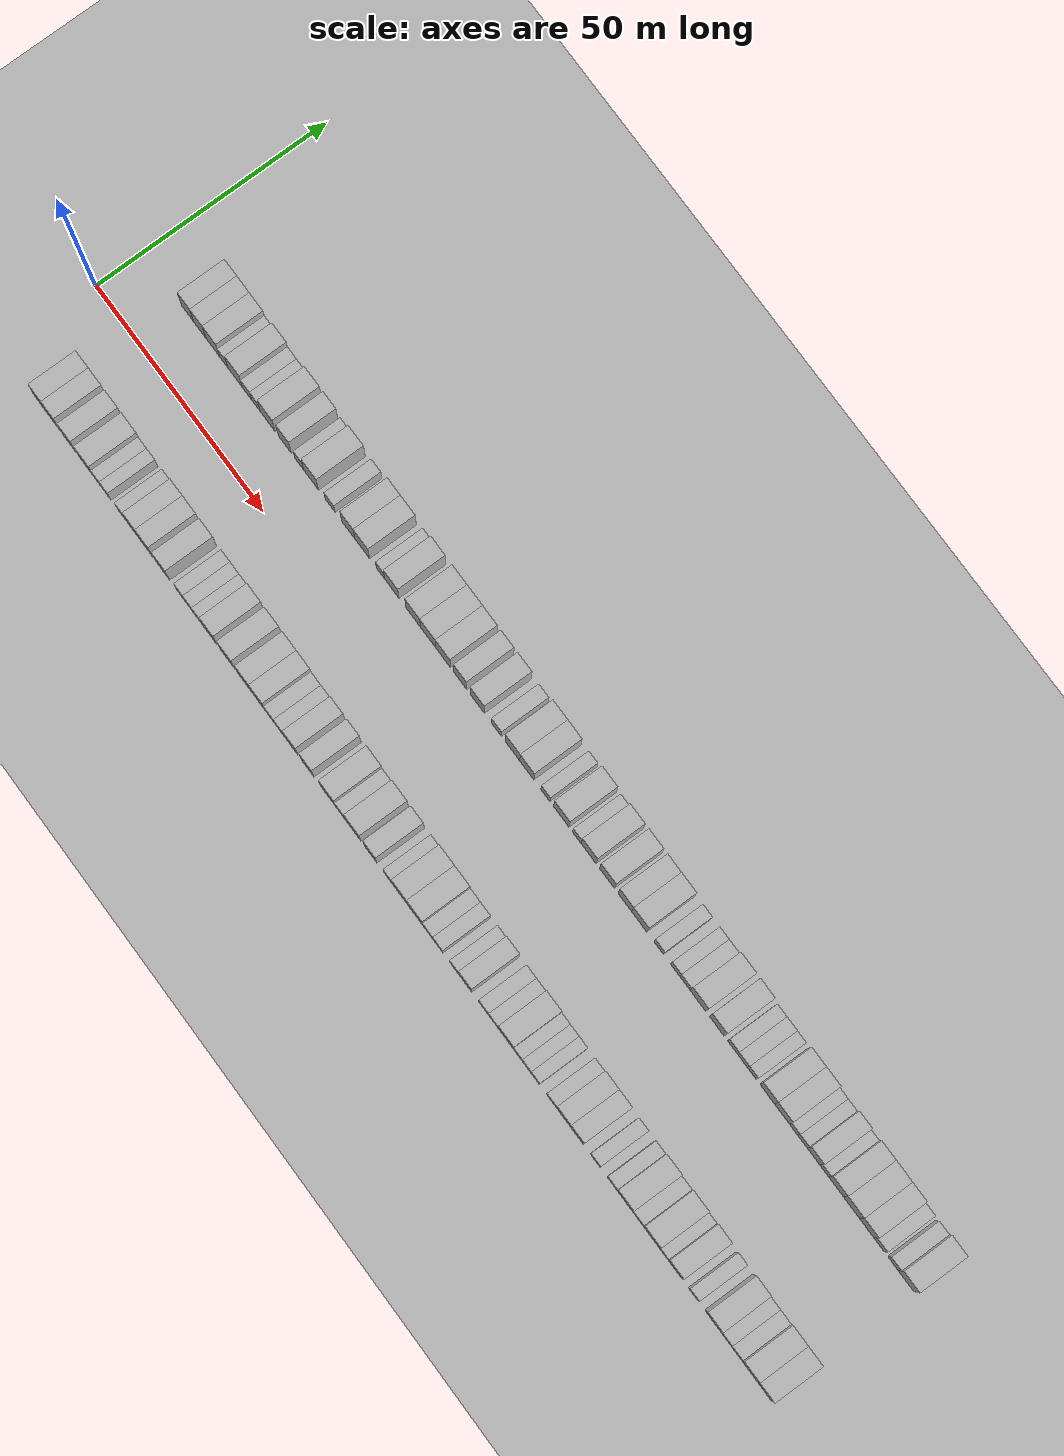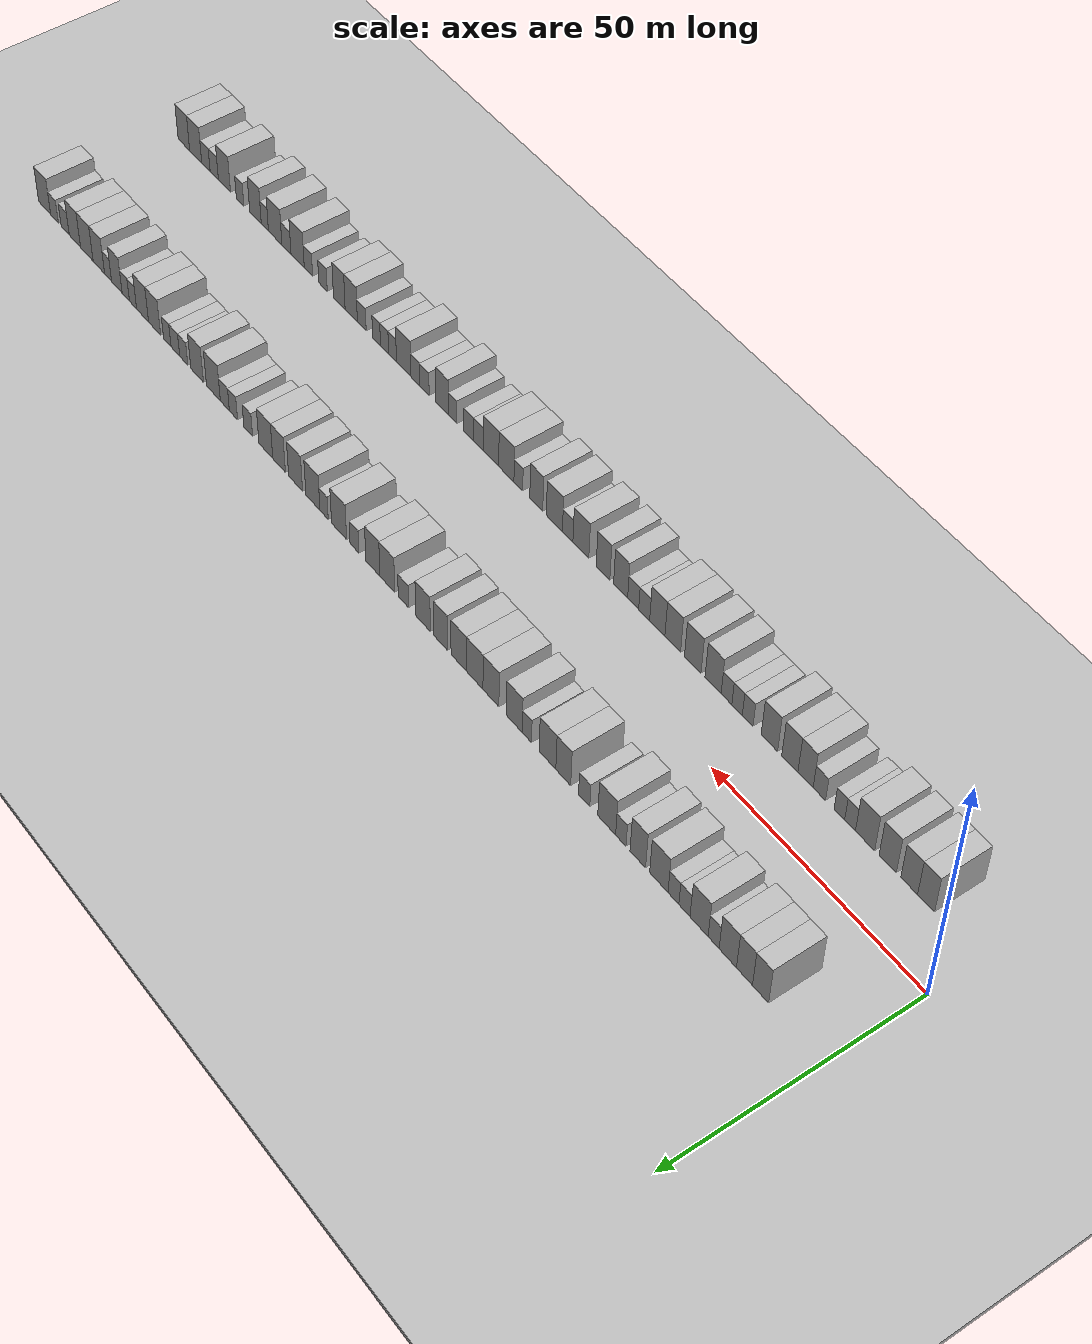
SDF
<?xml version="1.0" encoding="utf-8"?>

<sdf version="1.6">

   <world name="default">

      <gui fullscreen="0">

         <camera name="user_camera">

            <pose>-15 0 4.57585 0 0 0</pose>

            <view_controller>orbit</view_controller>

         </camera>

      </gui>

      <scene>

         <sky>

           <clouds>

             <speed>12</speed>

           </clouds>

         </sky>

         <ambient>0.4 0.4 0.4 1</ambient>

         <background>0.7 0.7 0.7 1</background>

         <shadows>1</shadows>

      </scene>

      <gravity>0 0 -9.8066</gravity>

      <magnetic_field>6e-06 2.3e-05 -4.2e-05</magnetic_field>

      <physics default="0" name="default_physics" type="ode">

         <ode>

            <solver>

               <type>quick</type>

               <iters>10</iters>

               <sor>1.0</sor>

               <use_dynamic_moi_rescaling>0</use_dynamic_moi_rescaling>

            </solver>

            <constraints>

               <cfm>0</cfm>

               <erp>0.2</erp>

               <contact_max_correcting_vel>100</contact_max_correcting_vel>

               <contact_surface_layer>0.001</contact_surface_layer>

            </constraints>

         </ode>

         <max_step_size>0.004</max_step_size>

         <real_time_factor>1</real_time_factor>

         <real_time_update_rate>250</real_time_update_rate>

      </physics>

      <light name="sun" type="directional">

         <cast_shadows>1</cast_shadows>

         <pose>0 0 10 0 0 0</pose>

         <diffuse>0.8 0.8 0.8 1</diffuse>

         <specular>0.2 0.2 0.2 1</specular>

         <attenuation>

            <range>1000</range>

            <constant>0.9</constant>

            <linear>0.01</linear>

            <quadratic>0.001</quadratic>

         </attenuation>

         <direction>-0.5 0.1 -0.9</direction>

      </light>

      <include>

         <name>ground_plane_1</name>

         <uri>model://HANNAS_ground_plane</uri>

         <pose>0 0 0  0 0 0</pose>

      </include>

      <include>

         <name>ground_plane_2</name>

         <uri>model://HANNAS_ground_plane</uri>

         <pose>100 0 0  0 0 0</pose>

      </include>

      <model name="building_1">

         <static>1</static>

         <pose frame="">13.8397 15.0000 0 0.000000 0.000000 1.570796</pose>

         <link name="link">

            <pose frame="">0 0 4.50 0 0 0</pose>

            <collision name="collision">

               <geometry>

                  <box>

                     <size>10.0000 3.6794 9.0000</size>

                  </box>

               </geometry>

               <max_contacts>10</max_contacts>

               <surface>

                  <contact>

                     <ode/>

                  </contact>

                  <bounce/>

                  <friction>

                     <torsional>

                        <ode/>

                     </torsional>

                     <ode/>

                  </friction>

               </surface>

            </collision>

            <visual name="visual">

               <cast_shadows>0</cast_shadows>

               <geometry>

                  <box>

                     <size>10.0000 3.6794 9.0000</size>

                  </box>

               </geometry>

               <material>

                  <script>

                     <uri>model://HANNAS_wall/materials/scripts</uri>

                     <uri>model://HANNAS_wall/materials/textures</uri>

                     <name>vrc/HANNAS_wall</name>

                  </script>

               </material>

            </visual>

            <self_collide>0</self_collide>

            <enable_wind>0</enable_wind>

            <kinematic>0</kinematic>

         </link>

      </model>

      <model name="building_2">

         <static>1</static>

         <pose frame="">17.5218 15.0000 0 0.000000 0.000000 1.570796</pose>

         <link name="link">

            <pose frame="">0 0 4.50 0 0 0</pose>

            <collision name="collision">

               <geometry>

                  <box>

                     <size>10.0000 3.6849 9.0000</size>

                  </box>

               </geometry>

               <max_contacts>10</max_contacts>

               <surface>

                  <contact>

                     <ode/>

                  </contact>

                  <bounce/>

                  <friction>

                     <torsional>

                        <ode/>

                     </torsional>

                     <ode/>

                  </friction>

               </surface>

            </collision>

            <visual name="visual">

               <cast_shadows>0</cast_shadows>

               <geometry>

                  <box>

                     <size>10.0000 3.6849 9.0000</size>

                  </box>

               </geometry>

               <material>

                  <script>

                     <uri>model://HANNAS_wall/materials/scripts</uri>

                     <uri>model://HANNAS_wall/materials/textures</uri>

                     <name>vrc/HANNAS_wall</name>

                  </script>

               </material>

            </visual>

            <self_collide>0</self_collide>

            <enable_wind>0</enable_wind>

            <kinematic>0</kinematic>

         </link>

      </model>

      <model name="building_3">

         <static>1</static>

         <pose frame="">21.3801 15.0000 0 0.000000 0.000000 1.570796</pose>

         <link name="link">

            <pose frame="">0 0 4.50 0 0 0</pose>

            <collision name="collision">

               <geometry>

                  <box>

                     <size>10.0000 4.0316 9.0000</size>

                  </box>

               </geometry>

               <max_contacts>10</max_contacts>

               <surface>

                  <contact>

                     <ode/>

                  </contact>

                  <bounce/>

                  <friction>

                     <torsional>

                        <ode/>

                     </torsional>

                     <ode/>

                  </friction>

               </surface>

            </collision>

            <visual name="visual">

               <cast_shadows>0</cast_shadows>

               <geometry>

                  <box>

                     <size>10.0000 4.0316 9.0000</size>

                  </box>

               </geometry>

               <material>

                  <script>

                     <uri>model://HANNAS_wall/materials/scripts</uri>

                     <uri>model://HANNAS_wall/materials/textures</uri>

                     <name>vrc/HANNAS_wall</name>

                  </script>

               </material>

            </visual>

            <self_collide>0</self_collide>

            <enable_wind>0</enable_wind>

            <kinematic>0</kinematic>

         </link>

      </model>

      <model name="building_4">

         <static>1</static>

         <pose frame="">24.6858 15.0000 0 0.000000 0.000000 1.570796</pose>

         <link name="link">

            <pose frame="">0 0 3.00 0 0 0</pose>

            <collision name="collision">

               <geometry>

                  <box>

                     <size>10.0000 2.5798 6.0000</size>

                  </box>

               </geometry>

               <max_contacts>10</max_contacts>

               <surface>

                  <contact>

                     <ode/>

                  </contact>

                  <bounce/>

                  <friction>

                     <torsional>

                        <ode/>

                     </torsional>

                     <ode/>

                  </friction>

               </surface>

            </collision>

            <visual name="visual">

               <cast_shadows>0</cast_shadows>

               <geometry>

                  <box>

                     <size>10.0000 2.5798 6.0000</size>

                  </box>

               </geometry>

               <material>

                  <script>

                     <uri>model://HANNAS_wall/materials/scripts</uri>

                     <uri>model://HANNAS_wall/materials/textures</uri>

                     <name>vrc/HANNAS_wall</name>

                  </script>

               </material>

            </visual>

            <self_collide>0</self_collide>

            <enable_wind>0</enable_wind>

            <kinematic>0</kinematic>

         </link>

      </model>

      <model name="building_5">

         <static>1</static>

         <pose frame="">28.1155 15.0000 0 0.000000 0.000000 1.570796</pose>

         <link name="link">

            <pose frame="">0 0 4.50 0 0 0</pose>

            <collision name="collision">

               <geometry>

                  <box>

                     <size>10.0000 4.2796 9.0000</size>

                  </box>

               </geometry>

               <max_contacts>10</max_contacts>

               <surface>

                  <contact>

                     <ode/>

                  </contact>

                  <bounce/>

                  <friction>

                     <torsional>

                        <ode/>

                     </torsional>

                     <ode/>

                  </friction>

               </surface>

            </collision>

            <visual name="visual">

               <cast_shadows>0</cast_shadows>

               <geometry>

                  <box>

                     <size>10.0000 4.2796 9.0000</size>

                  </box>

               </geometry>

               <material>

                  <script>

                     <uri>model://HANNAS_wall/materials/scripts</uri>

                     <uri>model://HANNAS_wall/materials/textures</uri>

                     <name>vrc/HANNAS_wall</name>

                  </script>

               </material>

            </visual>

            <self_collide>0</self_collide>

            <enable_wind>0</enable_wind>

            <kinematic>0</kinematic>

         </link>

      </model>

      <model name="building_6">

         <static>1</static>

         <pose frame="">31.5834 15.0000 0 0.000000 0.000000 1.570796</pose>

         <link name="link">

            <pose frame="">0 0 3.00 0 0 0</pose>

            <collision name="collision">

               <geometry>

                  <box>

                     <size>10.0000 2.6562 6.0000</size>

                  </box>

               </geometry>

               <max_contacts>10</max_contacts>

               <surface>

                  <contact>

                     <ode/>

                  </contact>

                  <bounce/>

                  <friction>

                     <torsional>

                        <ode/>

                     </torsional>

                     <ode/>

                  </friction>

               </surface>

            </collision>

            <visual name="visual">

               <cast_shadows>0</cast_shadows>

               <geometry>

                  <box>

                     <size>10.0000 2.6562 6.0000</size>

                  </box>

               </geometry>

               <material>

                  <script>

                     <uri>model://HANNAS_wall/materials/scripts</uri>

                     <uri>model://HANNAS_wall/materials/textures</uri>

                     <name>vrc/HANNAS_wall</name>

                  </script>

               </material>

            </visual>

            <self_collide>0</self_collide>

            <enable_wind>0</enable_wind>

            <kinematic>0</kinematic>

         </link>

      </model>

      <model name="building_7">

         <static>1</static>

         <pose frame="">34.2161 15.0000 0 0.000000 0.000000 1.570796</pose>

         <link name="link">

            <pose frame="">0 0 3.00 0 0 0</pose>

            <collision name="collision">

               <geometry>

                  <box>

                     <size>10.0000 2.6093 6.0000</size>

                  </box>

               </geometry>

               <max_contacts>10</max_contacts>

               <surface>

                  <contact>

                     <ode/>

                  </contact>

                  <bounce/>

                  <friction>

                     <torsional>

                        <ode/>

                     </torsional>

                     <ode/>

                  </friction>

               </surface>

            </collision>

            <visual name="visual">

               <cast_shadows>0</cast_shadows>

               <geometry>

                  <box>

                     <size>10.0000 2.6093 6.0000</size>

                  </box>

               </geometry>

               <material>

                  <script>

                     <uri>model://HANNAS_wall/materials/scripts</uri>

                     <uri>model://HANNAS_wall/materials/textures</uri>

                     <name>vrc/HANNAS_wall</name>

                  </script>

               </material>

            </visual>

            <self_collide>0</self_collide>

            <enable_wind>0</enable_wind>

            <kinematic>0</kinematic>

         </link>

      </model>

      <model name="building_8">

         <static>1</static>

         <pose frame="">37.7383 15.0000 0 0.000000 0.000000 1.570796</pose>

         <link name="link">

            <pose frame="">0 0 4.50 0 0 0</pose>

            <collision name="collision">

               <geometry>

                  <box>

                     <size>10.0000 4.4352 9.0000</size>

                  </box>

               </geometry>

               <max_contacts>10</max_contacts>

               <surface>

                  <contact>

                     <ode/>

                  </contact>

                  <bounce/>

                  <friction>

                     <torsional>

                        <ode/>

                     </torsional>

                     <ode/>

                  </friction>

               </surface>

            </collision>

            <visual name="visual">

               <cast_shadows>0</cast_shadows>

               <geometry>

                  <box>

                     <size>10.0000 4.4352 9.0000</size>

                  </box>

               </geometry>

               <material>

                  <script>

                     <uri>model://HANNAS_wall/materials/scripts</uri>

                     <uri>model://HANNAS_wall/materials/textures</uri>

                     <name>vrc/HANNAS_wall</name>

                  </script>

               </material>

            </visual>

            <self_collide>0</self_collide>

            <enable_wind>0</enable_wind>

            <kinematic>0</kinematic>

         </link>

      </model>

      <model name="building_9">

         <static>1</static>

         <pose frame="">42.8617 15.0000 0 0.000000 0.000000 1.570796</pose>

         <link name="link">

            <pose frame="">0 0 4.50 0 0 0</pose>

            <collision name="collision">

               <geometry>

                  <box>

                     <size>10.0000 3.8115 9.0000</size>

                  </box>

               </geometry>

               <max_contacts>10</max_contacts>

               <surface>

                  <contact>

                     <ode/>

                  </contact>

                  <bounce/>

                  <friction>

                     <torsional>

                        <ode/>

                     </torsional>

                     <ode/>

                  </friction>

               </surface>

            </collision>

            <visual name="visual">

               <cast_shadows>0</cast_shadows>

               <geometry>

                  <box>

                     <size>10.0000 3.8115 9.0000</size>

                  </box>

               </geometry>

               <material>

                  <script>

                     <uri>model://HANNAS_wall/materials/scripts</uri>

                     <uri>model://HANNAS_wall/materials/textures</uri>

                     <name>vrc/HANNAS_wall</name>

                  </script>

               </material>

            </visual>

            <self_collide>0</self_collide>

            <enable_wind>0</enable_wind>

            <kinematic>0</kinematic>

         </link>

      </model>

      <model name="building_10">

         <static>1</static>

         <pose frame="">47.0494 15.0000 0 0.000000 0.000000 1.570796</pose>

         <link name="link">

            <pose frame="">0 0 3.00 0 0 0</pose>

            <collision name="collision">

               <geometry>

                  <box>

                     <size>10.0000 2.5639 6.0000</size>

                  </box>

               </geometry>

               <max_contacts>10</max_contacts>

               <surface>

                  <contact>

                     <ode/>

                  </contact>

                  <bounce/>

                  <friction>

                     <torsional>

                        <ode/>

                     </torsional>

                     <ode/>

                  </friction>

               </surface>

            </collision>

            <visual name="visual">

               <cast_shadows>0</cast_shadows>

               <geometry>

                  <box>

                     <size>10.0000 2.5639 6.0000</size>

                  </box>

               </geometry>

               <material>

                  <script>

                     <uri>model://HANNAS_wall/materials/scripts</uri>

                     <uri>model://HANNAS_wall/materials/textures</uri>

                     <name>vrc/HANNAS_wall</name>

                  </script>

               </material>

            </visual>

            <self_collide>0</self_collide>

            <enable_wind>0</enable_wind>

            <kinematic>0</kinematic>

         </link>

      </model>

      <model name="building_11">

         <static>1</static>

         <pose frame="">50.5670 15.0000 0 0.000000 0.000000 1.570796</pose>

         <link name="link">

            <pose frame="">0 0 4.50 0 0 0</pose>

            <collision name="collision">

               <geometry>

                  <box>

                     <size>10.0000 4.4715 9.0000</size>

                  </box>

               </geometry>

               <max_contacts>10</max_contacts>

               <surface>

                  <contact>

                     <ode/>

                  </contact>

                  <bounce/>

                  <friction>

                     <torsional>

                        <ode/>

                     </torsional>

                     <ode/>

                  </friction>

               </surface>

            </collision>

            <visual name="visual">

               <cast_shadows>0</cast_shadows>

               <geometry>

                  <box>

                     <size>10.0000 4.4715 9.0000</size>

                  </box>

               </geometry>

               <material>

                  <script>

                     <uri>model://HANNAS_wall/materials/scripts</uri>

                     <uri>model://HANNAS_wall/materials/textures</uri>

                     <name>vrc/HANNAS_wall</name>

                  </script>

               </material>

            </visual>

            <self_collide>0</self_collide>

            <enable_wind>0</enable_wind>

            <kinematic>0</kinematic>

         </link>

      </model>

      <model name="building_12">

         <static>1</static>

         <pose frame="">56.2342 15.0000 0 0.000000 0.000000 1.570796</pose>

         <link name="link">

            <pose frame="">0 0 3.00 0 0 0</pose>

            <collision name="collision">

               <geometry>

                  <box>

                     <size>10.0000 2.8628 6.0000</size>

                  </box>

               </geometry>

               <max_contacts>10</max_contacts>

               <surface>

                  <contact>

                     <ode/>

                  </contact>

                  <bounce/>

                  <friction>

                     <torsional>

                        <ode/>

                     </torsional>

                     <ode/>

                  </friction>

               </surface>

            </collision>

            <visual name="visual">

               <cast_shadows>0</cast_shadows>

               <geometry>

                  <box>

                     <size>10.0000 2.8628 6.0000</size>

                  </box>

               </geometry>

               <material>

                  <script>

                     <uri>model://HANNAS_wall/materials/scripts</uri>

                     <uri>model://HANNAS_wall/materials/textures</uri>

                     <name>vrc/HANNAS_wall</name>

                  </script>

               </material>

            </visual>

            <self_collide>0</self_collide>

            <enable_wind>0</enable_wind>

            <kinematic>0</kinematic>

         </link>

      </model>

      <model name="building_13">

         <static>1</static>

         <pose frame="">61.5704 15.0000 0 0.000000 0.000000 1.570796</pose>

         <link name="link">

            <pose frame="">0 0 4.50 0 0 0</pose>

            <collision name="collision">

               <geometry>

                  <box>

                     <size>10.0000 3.8097 9.0000</size>

                  </box>

               </geometry>

               <max_contacts>10</max_contacts>

               <surface>

                  <contact>

                     <ode/>

                  </contact>

                  <bounce/>

                  <friction>

                     <torsional>

                        <ode/>

                     </torsional>

                     <ode/>

                  </friction>

               </surface>

            </collision>

            <visual name="visual">

               <cast_shadows>0</cast_shadows>

               <geometry>

                  <box>

                     <size>10.0000 3.8097 9.0000</size>

                  </box>

               </geometry>

               <material>

                  <script>

                     <uri>model://HANNAS_wall/materials/scripts</uri>

                     <uri>model://HANNAS_wall/materials/textures</uri>

                     <name>vrc/HANNAS_wall</name>

                  </script>

               </material>

            </visual>

            <self_collide>0</self_collide>

            <enable_wind>0</enable_wind>

            <kinematic>0</kinematic>

         </link>

      </model>

      <model name="building_14">

         <static>1</static>

         <pose frame="">65.6387 15.0000 0 0.000000 0.000000 1.570796</pose>

         <link name="link">

            <pose frame="">0 0 4.50 0 0 0</pose>

            <collision name="collision">

               <geometry>

                  <box>

                     <size>10.0000 4.3270 9.0000</size>

                  </box>

               </geometry>

               <max_contacts>10</max_contacts>

               <surface>

                  <contact>

                     <ode/>

                  </contact>

                  <bounce/>

                  <friction>

                     <torsional>

                        <ode/>

                     </torsional>

                     <ode/>

                  </friction>

               </surface>

            </collision>

            <visual name="visual">

               <cast_shadows>0</cast_shadows>

               <geometry>

                  <box>

                     <size>10.0000 4.3270 9.0000</size>

                  </box>

               </geometry>

               <material>

                  <script>

                     <uri>model://HANNAS_wall/materials/scripts</uri>

                     <uri>model://HANNAS_wall/materials/textures</uri>

                     <name>vrc/HANNAS_wall</name>

                  </script>

               </material>

            </visual>

            <self_collide>0</self_collide>

            <enable_wind>0</enable_wind>

            <kinematic>0</kinematic>

         </link>

      </model>

      <model name="building_15">

         <static>1</static>

         <pose frame="">71.0189 15.0000 0 0.000000 0.000000 1.570796</pose>

         <link name="link">

            <pose frame="">0 0 3.00 0 0 0</pose>

            <collision name="collision">

               <geometry>

                  <box>

                     <size>10.0000 2.4332 6.0000</size>

                  </box>

               </geometry>

               <max_contacts>10</max_contacts>

               <surface>

                  <contact>

                     <ode/>

                  </contact>

                  <bounce/>

                  <friction>

                     <torsional>

                        <ode/>

                     </torsional>

                     <ode/>

                  </friction>

               </surface>

            </collision>

            <visual name="visual">

               <cast_shadows>0</cast_shadows>

               <geometry>

                  <box>

                     <size>10.0000 2.4332 6.0000</size>

                  </box>

               </geometry>

               <material>

                  <script>

                     <uri>model://HANNAS_wall/materials/scripts</uri>

                     <uri>model://HANNAS_wall/materials/textures</uri>

                     <name>vrc/HANNAS_wall</name>

                  </script>

               </material>

            </visual>

            <self_collide>0</self_collide>

            <enable_wind>0</enable_wind>

            <kinematic>0</kinematic>

         </link>

      </model>

      <model name="building_16">

         <static>1</static>

         <pose frame="">74.3353 15.0000 0 0.000000 0.000000 1.570796</pose>

         <link name="link">

            <pose frame="">0 0 4.50 0 0 0</pose>

            <collision name="collision">

               <geometry>

                  <box>

                     <size>10.0000 4.1997 9.0000</size>

                  </box>

               </geometry>

               <max_contacts>10</max_contacts>

               <surface>

                  <contact>

                     <ode/>

                  </contact>

                  <bounce/>

                  <friction>

                     <torsional>

                        <ode/>

                     </torsional>

                     <ode/>

                  </friction>

               </surface>

            </collision>

            <visual name="visual">

               <cast_shadows>0</cast_shadows>

               <geometry>

                  <box>

                     <size>10.0000 4.1997 9.0000</size>

                  </box>

               </geometry>

               <material>

                  <script>

                     <uri>model://HANNAS_wall/materials/scripts</uri>

                     <uri>model://HANNAS_wall/materials/textures</uri>

                     <name>vrc/HANNAS_wall</name>

                  </script>

               </material>

            </visual>

            <self_collide>0</self_collide>

            <enable_wind>0</enable_wind>

            <kinematic>0</kinematic>

         </link>

      </model>

      <model name="building_17">

         <static>1</static>

         <pose frame="">80.5745 15.0000 0 0.000000 0.000000 1.570796</pose>

         <link name="link">

            <pose frame="">0 0 4.50 0 0 0</pose>

            <collision name="collision">

               <geometry>

                  <box>

                     <size>10.0000 4.2787 9.0000</size>

                  </box>

               </geometry>

               <max_contacts>10</max_contacts>

               <surface>

                  <contact>

                     <ode/>

                  </contact>

                  <bounce/>

                  <friction>

                     <torsional>

                        <ode/>

                     </torsional>

                     <ode/>

                  </friction>

               </surface>

            </collision>

            <visual name="visual">

               <cast_shadows>0</cast_shadows>

               <geometry>

                  <box>

                     <size>10.0000 4.2787 9.0000</size>

                  </box>

               </geometry>

               <material>

                  <script>

                     <uri>model://HANNAS_wall/materials/scripts</uri>

                     <uri>model://HANNAS_wall/materials/textures</uri>

                     <name>vrc/HANNAS_wall</name>

                  </script>

               </material>

            </visual>

            <self_collide>0</self_collide>

            <enable_wind>0</enable_wind>

            <kinematic>0</kinematic>

         </link>

      </model>

      <model name="building_18">

         <static>1</static>

         <pose frame="">84.9429 15.0000 0 0.000000 0.000000 1.570796</pose>

         <link name="link">

            <pose frame="">0 0 4.50 0 0 0</pose>

            <collision name="collision">

               <geometry>

                  <box>

                     <size>10.0000 4.4583 9.0000</size>

                  </box>

               </geometry>

               <max_contacts>10</max_contacts>

               <surface>

                  <contact>

                     <ode/>

                  </contact>

                  <bounce/>

                  <friction>

                     <torsional>

                        <ode/>

                     </torsional>

                     <ode/>

                  </friction>

               </surface>

            </collision>

            <visual name="visual">

               <cast_shadows>0</cast_shadows>

               <geometry>

                  <box>

                     <size>10.0000 4.4583 9.0000</size>

                  </box>

               </geometry>

               <material>

                  <script>

                     <uri>model://HANNAS_wall/materials/scripts</uri>

                     <uri>model://HANNAS_wall/materials/textures</uri>

                     <name>vrc/HANNAS_wall</name>

                  </script>

               </material>

            </visual>

            <self_collide>0</self_collide>

            <enable_wind>0</enable_wind>

            <kinematic>0</kinematic>

         </link>

      </model>

      <model name="building_19">

         <static>1</static>

         <pose frame="">89.2964 15.0000 0 0.000000 0.000000 1.570796</pose>

         <link name="link">

            <pose frame="">0 0 4.50 0 0 0</pose>

            <collision name="collision">

               <geometry>

                  <box>

                     <size>10.0000 4.2488 9.0000</size>

                  </box>

               </geometry>

               <max_contacts>10</max_contacts>

               <surface>

                  <contact>

                     <ode/>

                  </contact>

                  <bounce/>

                  <friction>

                     <torsional>

                        <ode/>

                     </torsional>

                     <ode/>

                  </friction>

               </surface>

            </collision>

            <visual name="visual">

               <cast_shadows>0</cast_shadows>

               <geometry>

                  <box>

                     <size>10.0000 4.2488 9.0000</size>

                  </box>

               </geometry>

               <material>

                  <script>

                     <uri>model://HANNAS_wall/materials/scripts</uri>

                     <uri>model://HANNAS_wall/materials/textures</uri>

                     <name>vrc/HANNAS_wall</name>

                  </script>

               </material>

            </visual>

            <self_collide>0</self_collide>

            <enable_wind>0</enable_wind>

            <kinematic>0</kinematic>

         </link>

      </model>

      <model name="building_20">

         <static>1</static>

         <pose frame="">94.2962 15.0000 0 0.000000 0.000000 1.570796</pose>

         <link name="link">

            <pose frame="">0 0 4.50 0 0 0</pose>

            <collision name="collision">

               <geometry>

                  <box>

                     <size>10.0000 3.7507 9.0000</size>

                  </box>

               </geometry>

               <max_contacts>10</max_contacts>

               <surface>

                  <contact>

                     <ode/>

                  </contact>

                  <bounce/>

                  <friction>

                     <torsional>

                        <ode/>

                     </torsional>

                     <ode/>

                  </friction>

               </surface>

            </collision>

            <visual name="visual">

               <cast_shadows>0</cast_shadows>

               <geometry>

                  <box>

                     <size>10.0000 3.7507 9.0000</size>

                  </box>

               </geometry>

               <material>

                  <script>

                     <uri>model://HANNAS_wall/materials/scripts</uri>

                     <uri>model://HANNAS_wall/materials/textures</uri>

                     <name>vrc/HANNAS_wall</name>

                  </script>

               </material>

            </visual>

            <self_collide>0</self_collide>

            <enable_wind>0</enable_wind>

            <kinematic>0</kinematic>

         </link>

      </model>

      <model name="building_21">

         <static>1</static>

         <pose frame="">99.2326 15.0000 0 0.000000 0.000000 1.570796</pose>

         <link name="link">

            <pose frame="">0 0 4.50 0 0 0</pose>

            <collision name="collision">

               <geometry>

                  <box>

                     <size>10.0000 4.1222 9.0000</size>

                  </box>

               </geometry>

               <max_contacts>10</max_contacts>

               <surface>

                  <contact>

                     <ode/>

                  </contact>

                  <bounce/>

                  <friction>

                     <torsional>

                        <ode/>

                     </torsional>

                     <ode/>

                  </friction>

               </surface>

            </collision>

            <visual name="visual">

               <cast_shadows>0</cast_shadows>

               <geometry>

                  <box>

                     <size>10.0000 4.1222 9.0000</size>

                  </box>

               </geometry>

               <material>

                  <script>

                     <uri>model://HANNAS_wall/materials/scripts</uri>

                     <uri>model://HANNAS_wall/materials/textures</uri>

                     <name>vrc/HANNAS_wall</name>

                  </script>

               </material>

            </visual>

            <self_collide>0</self_collide>

            <enable_wind>0</enable_wind>

            <kinematic>0</kinematic>

         </link>

      </model>

      <model name="building_22">

         <static>1</static>

         <pose frame="">104.7581 15.0000 0 0.000000 0.000000 1.570796</pose>

         <link name="link">

            <pose frame="">0 0 3.00 0 0 0</pose>

            <collision name="collision">

               <geometry>

                  <box>

                     <size>10.0000 2.9286 6.0000</size>

                  </box>

               </geometry>

               <max_contacts>10</max_contacts>

               <surface>

                  <contact>

                     <ode/>

                  </contact>

                  <bounce/>

                  <friction>

                     <torsional>

                        <ode/>

                     </torsional>

                     <ode/>

                  </friction>

               </surface>

            </collision>

            <visual name="visual">

               <cast_shadows>0</cast_shadows>

               <geometry>

                  <box>

                     <size>10.0000 2.9286 6.0000</size>

                  </box>

               </geometry>

               <material>

                  <script>

                     <uri>model://HANNAS_wall/materials/scripts</uri>

                     <uri>model://HANNAS_wall/materials/textures</uri>

                     <name>vrc/HANNAS_wall</name>

                  </script>

               </material>

            </visual>

            <self_collide>0</self_collide>

            <enable_wind>0</enable_wind>

            <kinematic>0</kinematic>

         </link>

      </model>

      <model name="building_23">

         <static>1</static>

         <pose frame="">109.3536 15.0000 0 0.000000 0.000000 1.570796</pose>

         <link name="link">

            <pose frame="">0 0 4.50 0 0 0</pose>

            <collision name="collision">

               <geometry>

                  <box>

                     <size>10.0000 4.2624 9.0000</size>

                  </box>

               </geometry>

               <max_contacts>10</max_contacts>

               <surface>

                  <contact>

                     <ode/>

                  </contact>

                  <bounce/>

                  <friction>

                     <torsional>

                        <ode/>

                     </torsional>

                     <ode/>

                  </friction>

               </surface>

            </collision>

            <visual name="visual">

               <cast_shadows>0</cast_shadows>

               <geometry>

                  <box>

                     <size>10.0000 4.2624 9.0000</size>

                  </box>

               </geometry>

               <material>

                  <script>

                     <uri>model://HANNAS_wall/materials/scripts</uri>

                     <uri>model://HANNAS_wall/materials/textures</uri>

                     <name>vrc/HANNAS_wall</name>

                  </script>

               </material>

            </visual>

            <self_collide>0</self_collide>

            <enable_wind>0</enable_wind>

            <kinematic>0</kinematic>

         </link>

      </model>

      <model name="building_24">

         <static>1</static>

         <pose frame="">113.5259 15.0000 0 0.000000 0.000000 1.570796</pose>

         <link name="link">

            <pose frame="">0 0 4.50 0 0 0</pose>

            <collision name="collision">

               <geometry>

                  <box>

                     <size>10.0000 4.0823 9.0000</size>

                  </box>

               </geometry>

               <max_contacts>10</max_contacts>

               <surface>

                  <contact>

                     <ode/>

                  </contact>

                  <bounce/>

                  <friction>

                     <torsional>

                        <ode/>

                     </torsional>

                     <ode/>

                  </friction>

               </surface>

            </collision>

            <visual name="visual">

               <cast_shadows>0</cast_shadows>

               <geometry>

                  <box>

                     <size>10.0000 4.0823 9.0000</size>

                  </box>

               </geometry>

               <material>

                  <script>

                     <uri>model://HANNAS_wall/materials/scripts</uri>

                     <uri>model://HANNAS_wall/materials/textures</uri>

                     <name>vrc/HANNAS_wall</name>

                  </script>

               </material>

            </visual>

            <self_collide>0</self_collide>

            <enable_wind>0</enable_wind>

            <kinematic>0</kinematic>

         </link>

      </model>

      <model name="building_25">

         <static>1</static>

         <pose frame="">118.8828 15.0000 0 0.000000 0.000000 1.570796</pose>

         <link name="link">

            <pose frame="">0 0 3.00 0 0 0</pose>

            <collision name="collision">

               <geometry>

                  <box>

                     <size>10.0000 2.6316 6.0000</size>

                  </box>

               </geometry>

               <max_contacts>10</max_contacts>

               <surface>

                  <contact>

                     <ode/>

                  </contact>

                  <bounce/>

                  <friction>

                     <torsional>

                        <ode/>

                     </torsional>

                     <ode/>

                  </friction>

               </surface>

            </collision>

            <visual name="visual">

               <cast_shadows>0</cast_shadows>

               <geometry>

                  <box>

                     <size>10.0000 2.6316 6.0000</size>

                  </box>

               </geometry>

               <material>

                  <script>

                     <uri>model://HANNAS_wall/materials/scripts</uri>

                     <uri>model://HANNAS_wall/materials/textures</uri>

                     <name>vrc/HANNAS_wall</name>

                  </script>

               </material>

            </visual>

            <self_collide>0</self_collide>

            <enable_wind>0</enable_wind>

            <kinematic>0</kinematic>

         </link>

      </model>

      <model name="building_26">

         <static>1</static>

         <pose frame="">123.4322 15.0000 0 0.000000 0.000000 1.570796</pose>

         <link name="link">

            <pose frame="">0 0 4.50 0 0 0</pose>

            <collision name="collision">

               <geometry>

                  <box>

                     <size>10.0000 4.4671 9.0000</size>

                  </box>

               </geometry>

               <max_contacts>10</max_contacts>

               <surface>

                  <contact>

                     <ode/>

                  </contact>

                  <bounce/>

                  <friction>

                     <torsional>

                        <ode/>

                     </torsional>

                     <ode/>

                  </friction>

               </surface>

            </collision>

            <visual name="visual">

               <cast_shadows>0</cast_shadows>

               <geometry>

                  <box>

                     <size>10.0000 4.4671 9.0000</size>

                  </box>

               </geometry>

               <material>

                  <script>

                     <uri>model://HANNAS_wall/materials/scripts</uri>

                     <uri>model://HANNAS_wall/materials/textures</uri>

                     <name>vrc/HANNAS_wall</name>

                  </script>

               </material>

            </visual>

            <self_collide>0</self_collide>

            <enable_wind>0</enable_wind>

            <kinematic>0</kinematic>

         </link>

      </model>

      <model name="building_27">

         <static>1</static>

         <pose frame="">127.9022 15.0000 0 0.000000 0.000000 1.570796</pose>

         <link name="link">

            <pose frame="">0 0 3.00 0 0 0</pose>

            <collision name="collision">

               <geometry>

                  <box>

                     <size>10.0000 2.4729 6.0000</size>

                  </box>

               </geometry>

               <max_contacts>10</max_contacts>

               <surface>

                  <contact>

                     <ode/>

                  </contact>

                  <bounce/>

                  <friction>

                     <torsional>

                        <ode/>

                     </torsional>

                     <ode/>

                  </friction>

               </surface>

            </collision>

            <visual name="visual">

               <cast_shadows>0</cast_shadows>

               <geometry>

                  <box>

                     <size>10.0000 2.4729 6.0000</size>

                  </box>

               </geometry>

               <material>

                  <script>

                     <uri>model://HANNAS_wall/materials/scripts</uri>

                     <uri>model://HANNAS_wall/materials/textures</uri>

                     <name>vrc/HANNAS_wall</name>

                  </script>

               </material>

            </visual>

            <self_collide>0</self_collide>

            <enable_wind>0</enable_wind>

            <kinematic>0</kinematic>

         </link>

      </model>

      <model name="building_28">

         <static>1</static>

         <pose frame="">131.2680 15.0000 0 0.000000 0.000000 1.570796</pose>

         <link name="link">

            <pose frame="">0 0 4.50 0 0 0</pose>

            <collision name="collision">

               <geometry>

                  <box>

                     <size>10.0000 4.2587 9.0000</size>

                  </box>

               </geometry>

               <max_contacts>10</max_contacts>

               <surface>

                  <contact>

                     <ode/>

                  </contact>

                  <bounce/>

                  <friction>

                     <torsional>

                        <ode/>

                     </torsional>

                     <ode/>

                  </friction>

               </surface>

            </collision>

            <visual name="visual">

               <cast_shadows>0</cast_shadows>

               <geometry>

                  <box>

                     <size>10.0000 4.2587 9.0000</size>

                  </box>

               </geometry>

               <material>

                  <script>

                     <uri>model://HANNAS_wall/materials/scripts</uri>

                     <uri>model://HANNAS_wall/materials/textures</uri>

                     <name>vrc/HANNAS_wall</name>

                  </script>

               </material>

            </visual>

            <self_collide>0</self_collide>

            <enable_wind>0</enable_wind>

            <kinematic>0</kinematic>

         </link>

      </model>

      <model name="building_29">

         <static>1</static>

         <pose frame="">136.5224 15.0000 0 0.000000 0.000000 1.570796</pose>

         <link name="link">

            <pose frame="">0 0 4.50 0 0 0</pose>

            <collision name="collision">

               <geometry>

                  <box>

                     <size>10.0000 4.2500 9.0000</size>

                  </box>

               </geometry>

               <max_contacts>10</max_contacts>

               <surface>

                  <contact>

                     <ode/>

                  </contact>

                  <bounce/>

                  <friction>

                     <torsional>

                        <ode/>

                     </torsional>

                     <ode/>

                  </friction>

               </surface>

            </collision>

            <visual name="visual">

               <cast_shadows>0</cast_shadows>

               <geometry>

                  <box>

                     <size>10.0000 4.2500 9.0000</size>

                  </box>

               </geometry>

               <material>

                  <script>

                     <uri>model://HANNAS_wall/materials/scripts</uri>

                     <uri>model://HANNAS_wall/materials/textures</uri>

                     <name>vrc/HANNAS_wall</name>

                  </script>

               </material>

            </visual>

            <self_collide>0</self_collide>

            <enable_wind>0</enable_wind>

            <kinematic>0</kinematic>

         </link>

      </model>

      <model name="building_30">

         <static>1</static>

         <pose frame="">141.5976 15.0000 0 0.000000 0.000000 1.570796</pose>

         <link name="link">

            <pose frame="">0 0 4.50 0 0 0</pose>

            <collision name="collision">

               <geometry>

                  <box>

                     <size>10.0000 3.9003 9.0000</size>

                  </box>

               </geometry>

               <max_contacts>10</max_contacts>

               <surface>

                  <contact>

                     <ode/>

                  </contact>

                  <bounce/>

                  <friction>

                     <torsional>

                        <ode/>

                     </torsional>

                     <ode/>

                  </friction>

               </surface>

            </collision>

            <visual name="visual">

               <cast_shadows>0</cast_shadows>

               <geometry>

                  <box>

                     <size>10.0000 3.9003 9.0000</size>

                  </box>

               </geometry>

               <material>

                  <script>

                     <uri>model://HANNAS_wall/materials/scripts</uri>

                     <uri>model://HANNAS_wall/materials/textures</uri>

                     <name>vrc/HANNAS_wall</name>

                  </script>

               </material>

            </visual>

            <self_collide>0</self_collide>

            <enable_wind>0</enable_wind>

            <kinematic>0</kinematic>

         </link>

      </model>

      <model name="building_31">

         <static>1</static>

         <pose frame="">145.7080 15.0000 0 0.000000 0.000000 1.570796</pose>

         <link name="link">

            <pose frame="">0 0 4.50 0 0 0</pose>

            <collision name="collision">

               <geometry>

                  <box>

                     <size>10.0000 4.3205 9.0000</size>

                  </box>

               </geometry>

               <max_contacts>10</max_contacts>

               <surface>

                  <contact>

                     <ode/>

                  </contact>

                  <bounce/>

                  <friction>

                     <torsional>

                        <ode/>

                     </torsional>

                     <ode/>

                  </friction>

               </surface>

            </collision>

            <visual name="visual">

               <cast_shadows>0</cast_shadows>

               <geometry>

                  <box>

                     <size>10.0000 4.3205 9.0000</size>

                  </box>

               </geometry>

               <material>

                  <script>

                     <uri>model://HANNAS_wall/materials/scripts</uri>

                     <uri>model://HANNAS_wall/materials/textures</uri>

                     <name>vrc/HANNAS_wall</name>

                  </script>

               </material>

            </visual>

            <self_collide>0</self_collide>

            <enable_wind>0</enable_wind>

            <kinematic>0</kinematic>

         </link>

      </model>

      <model name="building_32">

         <static>1</static>

         <pose frame="">151.2421 15.0000 0 0.000000 0.000000 1.570796</pose>

         <link name="link">

            <pose frame="">0 0 3.00 0 0 0</pose>

            <collision name="collision">

               <geometry>

                  <box>

                     <size>10.0000 2.7479 6.0000</size>

                  </box>

               </geometry>

               <max_contacts>10</max_contacts>

               <surface>

                  <contact>

                     <ode/>

                  </contact>

                  <bounce/>

                  <friction>

                     <torsional>

                        <ode/>

                     </torsional>

                     <ode/>

                  </friction>

               </surface>

            </collision>

            <visual name="visual">

               <cast_shadows>0</cast_shadows>

               <geometry>

                  <box>

                     <size>10.0000 2.7479 6.0000</size>

                  </box>

               </geometry>

               <material>

                  <script>

                     <uri>model://HANNAS_wall/materials/scripts</uri>

                     <uri>model://HANNAS_wall/materials/textures</uri>

                     <name>vrc/HANNAS_wall</name>

                  </script>

               </material>

            </visual>

            <self_collide>0</self_collide>

            <enable_wind>0</enable_wind>

            <kinematic>0</kinematic>

         </link>

      </model>

      <model name="building_33">

         <static>1</static>

         <pose frame="">155.9254 15.0000 0 0.000000 0.000000 1.570796</pose>

         <link name="link">

            <pose frame="">0 0 3.00 0 0 0</pose>

            <collision name="collision">

               <geometry>

                  <box>

                     <size>10.0000 2.6187 6.0000</size>

                  </box>

               </geometry>

               <max_contacts>10</max_contacts>

               <surface>

                  <contact>

                     <ode/>

                  </contact>

                  <bounce/>

                  <friction>

                     <torsional>

                        <ode/>

                     </torsional>

                     <ode/>

                  </friction>

               </surface>

            </collision>

            <visual name="visual">

               <cast_shadows>0</cast_shadows>

               <geometry>

                  <box>

                     <size>10.0000 2.6187 6.0000</size>

                  </box>

               </geometry>

               <material>

                  <script>

                     <uri>model://HANNAS_wall/materials/scripts</uri>

                     <uri>model://HANNAS_wall/materials/textures</uri>

                     <name>vrc/HANNAS_wall</name>

                  </script>

               </material>

            </visual>

            <self_collide>0</self_collide>

            <enable_wind>0</enable_wind>

            <kinematic>0</kinematic>

         </link>

      </model>

      <model name="building_34">

         <static>1</static>

         <pose frame="">158.6791 15.0000 0 0.000000 0.000000 1.570796</pose>

         <link name="link">

            <pose frame="">0 0 3.00 0 0 0</pose>

            <collision name="collision">

               <geometry>

                  <box>

                     <size>10.0000 2.8888 6.0000</size>

                  </box>

               </geometry>

               <max_contacts>10</max_contacts>

               <surface>

                  <contact>

                     <ode/>

                  </contact>

                  <bounce/>

                  <friction>

                     <torsional>

                        <ode/>

                     </torsional>

                     <ode/>

                  </friction>

               </surface>

            </collision>

            <visual name="visual">

               <cast_shadows>0</cast_shadows>

               <geometry>

                  <box>

                     <size>10.0000 2.8888 6.0000</size>

                  </box>

               </geometry>

               <material>

                  <script>

                     <uri>model://HANNAS_wall/materials/scripts</uri>

                     <uri>model://HANNAS_wall/materials/textures</uri>

                     <name>vrc/HANNAS_wall</name>

                  </script>

               </material>

            </visual>

            <self_collide>0</self_collide>

            <enable_wind>0</enable_wind>

            <kinematic>0</kinematic>

         </link>

      </model>

      <model name="building_35">

         <static>1</static>

         <pose frame="">162.3498 15.0000 0 0.000000 0.000000 1.570796</pose>

         <link name="link">

            <pose frame="">0 0 4.50 0 0 0</pose>

            <collision name="collision">

               <geometry>

                  <box>

                     <size>10.0000 4.4525 9.0000</size>

                  </box>

               </geometry>

               <max_contacts>10</max_contacts>

               <surface>

                  <contact>

                     <ode/>

                  </contact>

                  <bounce/>

                  <friction>

                     <torsional>

                        <ode/>

                     </torsional>

                     <ode/>

                  </friction>

               </surface>

            </collision>

            <visual name="visual">

               <cast_shadows>0</cast_shadows>

               <geometry>

                  <box>

                     <size>10.0000 4.4525 9.0000</size>

                  </box>

               </geometry>

               <material>

                  <script>

                     <uri>model://HANNAS_wall/materials/scripts</uri>

                     <uri>model://HANNAS_wall/materials/textures</uri>

                     <name>vrc/HANNAS_wall</name>

                  </script>

               </material>

            </visual>

            <self_collide>0</self_collide>

            <enable_wind>0</enable_wind>

            <kinematic>0</kinematic>

         </link>

      </model>

      <model name="building_36">

         <static>1</static>

         <pose frame="">167.6373 15.0000 0 0.000000 0.000000 1.570796</pose>

         <link name="link">

            <pose frame="">0 0 4.50 0 0 0</pose>

            <collision name="collision">

               <geometry>

                  <box>

                     <size>10.0000 4.1225 9.0000</size>

                  </box>

               </geometry>

               <max_contacts>10</max_contacts>

               <surface>

                  <contact>

                     <ode/>

                  </contact>

                  <bounce/>

                  <friction>

                     <torsional>

                        <ode/>

                     </torsional>

                     <ode/>

                  </friction>

               </surface>

            </collision>

            <visual name="visual">

               <cast_shadows>0</cast_shadows>

               <geometry>

                  <box>

                     <size>10.0000 4.1225 9.0000</size>

                  </box>

               </geometry>

               <material>

                  <script>

                     <uri>model://HANNAS_wall/materials/scripts</uri>

                     <uri>model://HANNAS_wall/materials/textures</uri>

                     <name>vrc/HANNAS_wall</name>

                  </script>

               </material>

            </visual>

            <self_collide>0</self_collide>

            <enable_wind>0</enable_wind>

            <kinematic>0</kinematic>

         </link>

      </model>

      <model name="building_37">

         <static>1</static>

         <pose frame="">172.0362 15.0000 0 0.000000 0.000000 1.570796</pose>

         <link name="link">

            <pose frame="">0 0 3.00 0 0 0</pose>

            <collision name="collision">

               <geometry>

                  <box>

                     <size>10.0000 2.6752 6.0000</size>

                  </box>

               </geometry>

               <max_contacts>10</max_contacts>

               <surface>

                  <contact>

                     <ode/>

                  </contact>

                  <bounce/>

                  <friction>

                     <torsional>

                        <ode/>

                     </torsional>

                     <ode/>

                  </friction>

               </surface>

            </collision>

            <visual name="visual">

               <cast_shadows>0</cast_shadows>

               <geometry>

                  <box>

                     <size>10.0000 2.6752 6.0000</size>

                  </box>

               </geometry>

               <material>

                  <script>

                     <uri>model://HANNAS_wall/materials/scripts</uri>

                     <uri>model://HANNAS_wall/materials/textures</uri>

                     <name>vrc/HANNAS_wall</name>

                  </script>

               </material>

            </visual>

            <self_collide>0</self_collide>

            <enable_wind>0</enable_wind>

            <kinematic>0</kinematic>

         </link>

      </model>

      <model name="building_38">

         <static>1</static>

         <pose frame="">174.8219 15.0000 0 0.000000 0.000000 1.570796</pose>

         <link name="link">

            <pose frame="">0 0 3.00 0 0 0</pose>

            <collision name="collision">

               <geometry>

                  <box>

                     <size>10.0000 2.8962 6.0000</size>

                  </box>

               </geometry>

               <max_contacts>10</max_contacts>

               <surface>

                  <contact>

                     <ode/>

                  </contact>

                  <bounce/>

                  <friction>

                     <torsional>

                        <ode/>

                     </torsional>

                     <ode/>

                  </friction>

               </surface>

            </collision>

            <visual name="visual">

               <cast_shadows>0</cast_shadows>

               <geometry>

                  <box>

                     <size>10.0000 2.8962 6.0000</size>

                  </box>

               </geometry>

               <material>

                  <script>

                     <uri>model://HANNAS_wall/materials/scripts</uri>

                     <uri>model://HANNAS_wall/materials/textures</uri>

                     <name>vrc/HANNAS_wall</name>

                  </script>

               </material>

            </visual>

            <self_collide>0</self_collide>

            <enable_wind>0</enable_wind>

            <kinematic>0</kinematic>

         </link>

      </model>

      <model name="building_39">

         <static>1</static>

         <pose frame="">177.5052 15.0000 0 0.000000 0.000000 1.570796</pose>

         <link name="link">

            <pose frame="">0 0 3.00 0 0 0</pose>

            <collision name="collision">

               <geometry>

                  <box>

                     <size>10.0000 2.4705 6.0000</size>

                  </box>

               </geometry>

               <max_contacts>10</max_contacts>

               <surface>

                  <contact>

                     <ode/>

                  </contact>

                  <bounce/>

                  <friction>

                     <torsional>

                        <ode/>

                     </torsional>

                     <ode/>

                  </friction>

               </surface>

            </collision>

            <visual name="visual">

               <cast_shadows>0</cast_shadows>

               <geometry>

                  <box>

                     <size>10.0000 2.4705 6.0000</size>

                  </box>

               </geometry>

               <material>

                  <script>

                     <uri>model://HANNAS_wall/materials/scripts</uri>

                     <uri>model://HANNAS_wall/materials/textures</uri>

                     <name>vrc/HANNAS_wall</name>

                  </script>

               </material>

            </visual>

            <self_collide>0</self_collide>

            <enable_wind>0</enable_wind>

            <kinematic>0</kinematic>

         </link>

      </model>

      <model name="building_40">

         <static>1</static>

         <pose frame="">181.7657 15.0000 0 0.000000 0.000000 1.570796</pose>

         <link name="link">

            <pose frame="">0 0 4.50 0 0 0</pose>

            <collision name="collision">

               <geometry>

                  <box>

                     <size>10.0000 4.0505 9.0000</size>

                  </box>

               </geometry>

               <max_contacts>10</max_contacts>

               <surface>

                  <contact>

                     <ode/>

                  </contact>

                  <bounce/>

                  <friction>

                     <torsional>

                        <ode/>

                     </torsional>

                     <ode/>

                  </friction>

               </surface>

            </collision>

            <visual name="visual">

               <cast_shadows>0</cast_shadows>

               <geometry>

                  <box>

                     <size>10.0000 4.0505 9.0000</size>

                  </box>

               </geometry>

               <material>

                  <script>

                     <uri>model://HANNAS_wall/materials/scripts</uri>

                     <uri>model://HANNAS_wall/materials/textures</uri>

                     <name>vrc/HANNAS_wall</name>

                  </script>

               </material>

            </visual>

            <self_collide>0</self_collide>

            <enable_wind>0</enable_wind>

            <kinematic>0</kinematic>

         </link>

      </model>

      <model name="building_41">

         <static>1</static>

         <pose frame="">185.8350 15.0000 0 0.000000 0.000000 1.570796</pose>

         <link name="link">

            <pose frame="">0 0 4.50 0 0 0</pose>

            <collision name="collision">

               <geometry>

                  <box>

                     <size>10.0000 4.0880 9.0000</size>

                  </box>

               </geometry>

               <max_contacts>10</max_contacts>

               <surface>

                  <contact>

                     <ode/>

                  </contact>

                  <bounce/>

                  <friction>

                     <torsional>

                        <ode/>

                     </torsional>

                     <ode/>

                  </friction>

               </surface>

            </collision>

            <visual name="visual">

               <cast_shadows>0</cast_shadows>

               <geometry>

                  <box>

                     <size>10.0000 4.0880 9.0000</size>

                  </box>

               </geometry>

               <material>

                  <script>

                     <uri>model://HANNAS_wall/materials/scripts</uri>

                     <uri>model://HANNAS_wall/materials/textures</uri>

                     <name>vrc/HANNAS_wall</name>

                  </script>

               </material>

            </visual>

            <self_collide>0</self_collide>

            <enable_wind>0</enable_wind>

            <kinematic>0</kinematic>

         </link>

      </model>

      <model name="building_42">

         <static>1</static>

         <pose frame="">189.0985 15.0000 0 0.000000 0.000000 1.570796</pose>

         <link name="link">

            <pose frame="">0 0 3.00 0 0 0</pose>

            <collision name="collision">

               <geometry>

                  <box>

                     <size>10.0000 2.4391 6.0000</size>

                  </box>

               </geometry>

               <max_contacts>10</max_contacts>

               <surface>

                  <contact>

                     <ode/>

                  </contact>

                  <bounce/>

                  <friction>

                     <torsional>

                        <ode/>

                     </torsional>

                     <ode/>

                  </friction>

               </surface>

            </collision>

            <visual name="visual">

               <cast_shadows>0</cast_shadows>

               <geometry>

                  <box>

                     <size>10.0000 2.4391 6.0000</size>

                  </box>

               </geometry>

               <material>

                  <script>

                     <uri>model://HANNAS_wall/materials/scripts</uri>

                     <uri>model://HANNAS_wall/materials/textures</uri>

                     <name>vrc/HANNAS_wall</name>

                  </script>

               </material>

            </visual>

            <self_collide>0</self_collide>

            <enable_wind>0</enable_wind>

            <kinematic>0</kinematic>

         </link>

      </model>

      <model name="building_43">

         <static>1</static>

         <pose frame="">191.5861 15.0000 0 0.000000 0.000000 1.570796</pose>

         <link name="link">

            <pose frame="">0 0 3.00 0 0 0</pose>

            <collision name="collision">

               <geometry>

                  <box>

                     <size>10.0000 2.5361 6.0000</size>

                  </box>

               </geometry>

               <max_contacts>10</max_contacts>

               <surface>

                  <contact>

                     <ode/>

                  </contact>

                  <bounce/>

                  <friction>

                     <torsional>

                        <ode/>

                     </torsional>

                     <ode/>

                  </friction>

               </surface>

            </collision>

            <visual name="visual">

               <cast_shadows>0</cast_shadows>

               <geometry>

                  <box>

                     <size>10.0000 2.5361 6.0000</size>

                  </box>

               </geometry>

               <material>

                  <script>

                     <uri>model://HANNAS_wall/materials/scripts</uri>

                     <uri>model://HANNAS_wall/materials/textures</uri>

                     <name>vrc/HANNAS_wall</name>

                  </script>

               </material>

            </visual>

            <self_collide>0</self_collide>

            <enable_wind>0</enable_wind>

            <kinematic>0</kinematic>

         </link>

      </model>

      <model name="building_44">

         <static>1</static>

         <pose frame="">194.6744 15.0000 0 0.000000 0.000000 1.570796</pose>

         <link name="link">

            <pose frame="">0 0 4.50 0 0 0</pose>

            <collision name="collision">

               <geometry>

                  <box>

                     <size>10.0000 3.6403 9.0000</size>

                  </box>

               </geometry>

               <max_contacts>10</max_contacts>

               <surface>

                  <contact>

                     <ode/>

                  </contact>

                  <bounce/>

                  <friction>

                     <torsional>

                        <ode/>

                     </torsional>

                     <ode/>

                  </friction>

               </surface>

            </collision>

            <visual name="visual">

               <cast_shadows>0</cast_shadows>

               <geometry>

                  <box>

                     <size>10.0000 3.6403 9.0000</size>

                  </box>

               </geometry>

               <material>

                  <script>

                     <uri>model://HANNAS_wall/materials/scripts</uri>

                     <uri>model://HANNAS_wall/materials/textures</uri>

                     <name>vrc/HANNAS_wall</name>

                  </script>

               </material>

            </visual>

            <self_collide>0</self_collide>

            <enable_wind>0</enable_wind>

            <kinematic>0</kinematic>

         </link>

      </model>

      <model name="building_45">

         <static>1</static>

         <pose frame="">197.7072 15.0000 0 0.000000 0.000000 1.570796</pose>

         <link name="link">

            <pose frame="">0 0 3.00 0 0 0</pose>

            <collision name="collision">

               <geometry>

                  <box>

                     <size>10.0000 2.4253 6.0000</size>

                  </box>

               </geometry>

               <max_contacts>10</max_contacts>

               <surface>

                  <contact>

                     <ode/>

                  </contact>

                  <bounce/>

                  <friction>

                     <torsional>

                        <ode/>

                     </torsional>

                     <ode/>

                  </friction>

               </surface>

            </collision>

            <visual name="visual">

               <cast_shadows>0</cast_shadows>

               <geometry>

                  <box>

                     <size>10.0000 2.4253 6.0000</size>

                  </box>

               </geometry>

               <material>

                  <script>

                     <uri>model://HANNAS_wall/materials/scripts</uri>

                     <uri>model://HANNAS_wall/materials/textures</uri>

                     <name>vrc/HANNAS_wall</name>

                  </script>

               </material>

            </visual>

            <self_collide>0</self_collide>

            <enable_wind>0</enable_wind>

            <kinematic>0</kinematic>

         </link>

      </model>

      <model name="building_46">

         <static>1</static>

         <pose frame="">200.9372 15.0000 0 0.000000 0.000000 1.570796</pose>

         <link name="link">

            <pose frame="">0 0 4.50 0 0 0</pose>

            <collision name="collision">

               <geometry>

                  <box>

                     <size>10.0000 4.0347 9.0000</size>

                  </box>

               </geometry>

               <max_contacts>10</max_contacts>

               <surface>

                  <contact>

                     <ode/>

                  </contact>

                  <bounce/>

                  <friction>

                     <torsional>

                        <ode/>

                     </torsional>

                     <ode/>

                  </friction>

               </surface>

            </collision>

            <visual name="visual">

               <cast_shadows>0</cast_shadows>

               <geometry>

                  <box>

                     <size>10.0000 4.0347 9.0000</size>

                  </box>

               </geometry>

               <material>

                  <script>

                     <uri>model://HANNAS_wall/materials/scripts</uri>

                     <uri>model://HANNAS_wall/materials/textures</uri>

                     <name>vrc/HANNAS_wall</name>

                  </script>

               </material>

            </visual>

            <self_collide>0</self_collide>

            <enable_wind>0</enable_wind>

            <kinematic>0</kinematic>

         </link>

      </model>

      <model name="building_47">

         <static>1</static>

         <pose frame="">205.1812 15.0000 0 0.000000 0.000000 1.570796</pose>

         <link name="link">

            <pose frame="">0 0 4.50 0 0 0</pose>

            <collision name="collision">

               <geometry>

                  <box>

                     <size>10.0000 4.4534 9.0000</size>

                  </box>

               </geometry>

               <max_contacts>10</max_contacts>

               <surface>

                  <contact>

                     <ode/>

                  </contact>

                  <bounce/>

                  <friction>

                     <torsional>

                        <ode/>

                     </torsional>

                     <ode/>

                  </friction>

               </surface>

            </collision>

            <visual name="visual">

               <cast_shadows>0</cast_shadows>

               <geometry>

                  <box>

                     <size>10.0000 4.4534 9.0000</size>

                  </box>

               </geometry>

               <material>

                  <script>

                     <uri>model://HANNAS_wall/materials/scripts</uri>

                     <uri>model://HANNAS_wall/materials/textures</uri>

                     <name>vrc/HANNAS_wall</name>

                  </script>

               </material>

            </visual>

            <self_collide>0</self_collide>

            <enable_wind>0</enable_wind>

            <kinematic>0</kinematic>

         </link>

      </model>

      <model name="building_48">

         <static>1</static>

         <pose frame="">209.4274 15.0000 0 0.000000 0.000000 1.570796</pose>

         <link name="link">

            <pose frame="">0 0 4.50 0 0 0</pose>

            <collision name="collision">

               <geometry>

                  <box>

                     <size>10.0000 4.0390 9.0000</size>

                  </box>

               </geometry>

               <max_contacts>10</max_contacts>

               <surface>

                  <contact>

                     <ode/>

                  </contact>

                  <bounce/>

                  <friction>

                     <torsional>

                        <ode/>

                     </torsional>

                     <ode/>

                  </friction>

               </surface>

            </collision>

            <visual name="visual">

               <cast_shadows>0</cast_shadows>

               <geometry>

                  <box>

                     <size>10.0000 4.0390 9.0000</size>

                  </box>

               </geometry>

               <material>

                  <script>

                     <uri>model://HANNAS_wall/materials/scripts</uri>

                     <uri>model://HANNAS_wall/materials/textures</uri>

                     <name>vrc/HANNAS_wall</name>

                  </script>

               </material>

            </visual>

            <self_collide>0</self_collide>

            <enable_wind>0</enable_wind>

            <kinematic>0</kinematic>

         </link>

      </model>

      <model name="building_49">

         <static>1</static>

         <pose frame="">212.8988 15.0000 0 0.000000 0.000000 1.570796</pose>

         <link name="link">

            <pose frame="">0 0 3.00 0 0 0</pose>

            <collision name="collision">

               <geometry>

                  <box>

                     <size>10.0000 2.9038 6.0000</size>

                  </box>

               </geometry>

               <max_contacts>10</max_contacts>

               <surface>

                  <contact>

                     <ode/>

                  </contact>

                  <bounce/>

                  <friction>

                     <torsional>

                        <ode/>

                     </torsional>

                     <ode/>

                  </friction>

               </surface>

            </collision>

            <visual name="visual">

               <cast_shadows>0</cast_shadows>

               <geometry>

                  <box>

                     <size>10.0000 2.9038 6.0000</size>

                  </box>

               </geometry>

               <material>

                  <script>

                     <uri>model://HANNAS_wall/materials/scripts</uri>

                     <uri>model://HANNAS_wall/materials/textures</uri>

                     <name>vrc/HANNAS_wall</name>

                  </script>

               </material>

            </visual>

            <self_collide>0</self_collide>

            <enable_wind>0</enable_wind>

            <kinematic>0</kinematic>

         </link>

      </model>

      <model name="building_50">

         <static>1</static>

         <pose frame="">216.7484 15.0000 0 0.000000 0.000000 1.570796</pose>

         <link name="link">

            <pose frame="">0 0 3.00 0 0 0</pose>

            <collision name="collision">

               <geometry>

                  <box>

                     <size>10.0000 2.7955 6.0000</size>

                  </box>

               </geometry>

               <max_contacts>10</max_contacts>

               <surface>

                  <contact>

                     <ode/>

                  </contact>

                  <bounce/>

                  <friction>

                     <torsional>

                        <ode/>

                     </torsional>

                     <ode/>

                  </friction>

               </surface>

            </collision>

            <visual name="visual">

               <cast_shadows>0</cast_shadows>

               <geometry>

                  <box>

                     <size>10.0000 2.7955 6.0000</size>

                  </box>

               </geometry>

               <material>

                  <script>

                     <uri>model://HANNAS_wall/materials/scripts</uri>

                     <uri>model://HANNAS_wall/materials/textures</uri>

                     <name>vrc/HANNAS_wall</name>

                  </script>

               </material>

            </visual>

            <self_collide>0</self_collide>

            <enable_wind>0</enable_wind>

            <kinematic>0</kinematic>

         </link>

      </model>

      <model name="building_51">

         <static>1</static>

         <pose frame="">220.3315 15.0000 0 0.000000 0.000000 1.570796</pose>

         <link name="link">

            <pose frame="">0 0 4.50 0 0 0</pose>

            <collision name="collision">

               <geometry>

                  <box>

                     <size>10.0000 4.3706 9.0000</size>

                  </box>

               </geometry>

               <max_contacts>10</max_contacts>

               <surface>

                  <contact>

                     <ode/>

                  </contact>

                  <bounce/>

                  <friction>

                     <torsional>

                        <ode/>

                     </torsional>

                     <ode/>

                  </friction>

               </surface>

            </collision>

            <visual name="visual">

               <cast_shadows>0</cast_shadows>

               <geometry>

                  <box>

                     <size>10.0000 4.3706 9.0000</size>

                  </box>

               </geometry>

               <material>

                  <script>

                     <uri>model://HANNAS_wall/materials/scripts</uri>

                     <uri>model://HANNAS_wall/materials/textures</uri>

                     <name>vrc/HANNAS_wall</name>

                  </script>

               </material>

            </visual>

            <self_collide>0</self_collide>

            <enable_wind>0</enable_wind>

            <kinematic>0</kinematic>

         </link>

      </model>

      <model name="building_52">

         <static>1</static>

         <pose frame="">11.8952 -15.0000 0 0.000000 0.000000 1.570796</pose>

         <link name="link">

            <pose frame="">0 0 4.50 0 0 0</pose>

            <collision name="collision">

               <geometry>

                  <box>

                     <size>10.0000 3.7903 9.0000</size>

                  </box>

               </geometry>

               <max_contacts>10</max_contacts>

               <surface>

                  <contact>

                     <ode/>

                  </contact>

                  <bounce/>

                  <friction>

                     <torsional>

                        <ode/>

                     </torsional>

                     <ode/>

                  </friction>

               </surface>

            </collision>

            <visual name="visual">

               <cast_shadows>0</cast_shadows>

               <geometry>

                  <box>

                     <size>10.0000 3.7903 9.0000</size>

                  </box>

               </geometry>

               <material>

                  <script>

                     <uri>model://HANNAS_wall/materials/scripts</uri>

                     <uri>model://HANNAS_wall/materials/textures</uri>

                     <name>vrc/HANNAS_wall</name>

                  </script>

               </material>

            </visual>

            <self_collide>0</self_collide>

            <enable_wind>0</enable_wind>

            <kinematic>0</kinematic>

         </link>

      </model>

      <model name="building_53">

         <static>1</static>

         <pose frame="">15.6842 -15.0000 0 0.000000 0.000000 1.570796</pose>

         <link name="link">

            <pose frame="">0 0 4.50 0 0 0</pose>

            <collision name="collision">

               <geometry>

                  <box>

                     <size>10.0000 3.7877 9.0000</size>

                  </box>

               </geometry>

               <max_contacts>10</max_contacts>

               <surface>

                  <contact>

                     <ode/>

                  </contact>

                  <bounce/>

                  <friction>

                     <torsional>

                        <ode/>

                     </torsional>

                     <ode/>

                  </friction>

               </surface>

            </collision>

            <visual name="visual">

               <cast_shadows>0</cast_shadows>

               <geometry>

                  <box>

                     <size>10.0000 3.7877 9.0000</size>

                  </box>

               </geometry>

               <material>

                  <script>

                     <uri>model://HANNAS_wall/materials/scripts</uri>

                     <uri>model://HANNAS_wall/materials/textures</uri>

                     <name>vrc/HANNAS_wall</name>

                  </script>

               </material>

            </visual>

            <self_collide>0</self_collide>

            <enable_wind>0</enable_wind>

            <kinematic>0</kinematic>

         </link>

      </model>

      <model name="building_54">

         <static>1</static>

         <pose frame="">20.5455 -15.0000 0 0.000000 0.000000 1.570796</pose>

         <link name="link">

            <pose frame="">0 0 4.50 0 0 0</pose>

            <collision name="collision">

               <geometry>

                  <box>

                     <size>10.0000 3.9350 9.0000</size>

                  </box>

               </geometry>

               <max_contacts>10</max_contacts>

               <surface>

                  <contact>

                     <ode/>

                  </contact>

                  <bounce/>

                  <friction>

                     <torsional>

                        <ode/>

                     </torsional>

                     <ode/>

                  </friction>

               </surface>

            </collision>

            <visual name="visual">

               <cast_shadows>0</cast_shadows>

               <geometry>

                  <box>

                     <size>10.0000 3.9350 9.0000</size>

                  </box>

               </geometry>

               <material>

                  <script>

                     <uri>model://HANNAS_wall/materials/scripts</uri>

                     <uri>model://HANNAS_wall/materials/textures</uri>

                     <name>vrc/HANNAS_wall</name>

                  </script>

               </material>

            </visual>

            <self_collide>0</self_collide>

            <enable_wind>0</enable_wind>

            <kinematic>0</kinematic>

         </link>

      </model>

      <model name="building_55">

         <static>1</static>

         <pose frame="">25.7320 -15.0000 0 0.000000 0.000000 1.570796</pose>

         <link name="link">

            <pose frame="">0 0 4.50 0 0 0</pose>

            <collision name="collision">

               <geometry>

                  <box>

                     <size>10.0000 4.4380 9.0000</size>

                  </box>

               </geometry>

               <max_contacts>10</max_contacts>

               <surface>

                  <contact>

                     <ode/>

                  </contact>

                  <bounce/>

                  <friction>

                     <torsional>

                        <ode/>

                     </torsional>

                     <ode/>

                  </friction>

               </surface>

            </collision>

            <visual name="visual">

               <cast_shadows>0</cast_shadows>

               <geometry>

                  <box>

                     <size>10.0000 4.4380 9.0000</size>

                  </box>

               </geometry>

               <material>

                  <script>

                     <uri>model://HANNAS_wall/materials/scripts</uri>

                     <uri>model://HANNAS_wall/materials/textures</uri>

                     <name>vrc/HANNAS_wall</name>

                  </script>

               </material>

            </visual>

            <self_collide>0</self_collide>

            <enable_wind>0</enable_wind>

            <kinematic>0</kinematic>

         </link>

      </model>

      <model name="building_56">

         <static>1</static>

         <pose frame="">29.2053 -15.0000 0 0.000000 0.000000 1.570796</pose>

         <link name="link">

            <pose frame="">0 0 3.00 0 0 0</pose>

            <collision name="collision">

               <geometry>

                  <box>

                     <size>10.0000 2.5085 6.0000</size>

                  </box>

               </geometry>

               <max_contacts>10</max_contacts>

               <surface>

                  <contact>

                     <ode/>

                  </contact>

                  <bounce/>

                  <friction>

                     <torsional>

                        <ode/>

                     </torsional>

                     <ode/>

                  </friction>

               </surface>

            </collision>

            <visual name="visual">

               <cast_shadows>0</cast_shadows>

               <geometry>

                  <box>

                     <size>10.0000 2.5085 6.0000</size>

                  </box>

               </geometry>

               <material>

                  <script>

                     <uri>model://HANNAS_wall/materials/scripts</uri>

                     <uri>model://HANNAS_wall/materials/textures</uri>

                     <name>vrc/HANNAS_wall</name>

                  </script>

               </material>

            </visual>

            <self_collide>0</self_collide>

            <enable_wind>0</enable_wind>

            <kinematic>0</kinematic>

         </link>

      </model>

      <model name="building_57">

         <static>1</static>

         <pose frame="">31.7024 -15.0000 0 0.000000 0.000000 1.570796</pose>

         <link name="link">

            <pose frame="">0 0 3.00 0 0 0</pose>

            <collision name="collision">

               <geometry>

                  <box>

                     <size>10.0000 2.4858 6.0000</size>

                  </box>

               </geometry>

               <max_contacts>10</max_contacts>

               <surface>

                  <contact>

                     <ode/>

                  </contact>

                  <bounce/>

                  <friction>

                     <torsional>

                        <ode/>

                     </torsional>

                     <ode/>

                  </friction>

               </surface>

            </collision>

            <visual name="visual">

               <cast_shadows>0</cast_shadows>

               <geometry>

                  <box>

                     <size>10.0000 2.4858 6.0000</size>

                  </box>

               </geometry>

               <material>

                  <script>

                     <uri>model://HANNAS_wall/materials/scripts</uri>

                     <uri>model://HANNAS_wall/materials/textures</uri>

                     <name>vrc/HANNAS_wall</name>

                  </script>

               </material>

            </visual>

            <self_collide>0</self_collide>

            <enable_wind>0</enable_wind>

            <kinematic>0</kinematic>

         </link>

      </model>

      <model name="building_58">

         <static>1</static>

         <pose frame="">36.4088 -15.0000 0 0.000000 0.000000 1.570796</pose>

         <link name="link">

            <pose frame="">0 0 3.00 0 0 0</pose>

            <collision name="collision">

               <geometry>

                  <box>

                     <size>10.0000 2.9269 6.0000</size>

                  </box>

               </geometry>

               <max_contacts>10</max_contacts>

               <surface>

                  <contact>

                     <ode/>

                  </contact>

                  <bounce/>

                  <friction>

                     <torsional>

                        <ode/>

                     </torsional>

                     <ode/>

                  </friction>

               </surface>

            </collision>

            <visual name="visual">

               <cast_shadows>0</cast_shadows>

               <geometry>

                  <box>

                     <size>10.0000 2.9269 6.0000</size>

                  </box>

               </geometry>

               <material>

                  <script>

                     <uri>model://HANNAS_wall/materials/scripts</uri>

                     <uri>model://HANNAS_wall/materials/textures</uri>

                     <name>vrc/HANNAS_wall</name>

                  </script>

               </material>

            </visual>

            <self_collide>0</self_collide>

            <enable_wind>0</enable_wind>

            <kinematic>0</kinematic>

         </link>

      </model>

      <model name="building_59">

         <static>1</static>

         <pose frame="">39.6919 -15.0000 0 0.000000 0.000000 1.570796</pose>

         <link name="link">

            <pose frame="">0 0 4.50 0 0 0</pose>

            <collision name="collision">

               <geometry>

                  <box>

                     <size>10.0000 3.6393 9.0000</size>

                  </box>

               </geometry>

               <max_contacts>10</max_contacts>

               <surface>

                  <contact>

                     <ode/>

                  </contact>

                  <bounce/>

                  <friction>

                     <torsional>

                        <ode/>

                     </torsional>

                     <ode/>

                  </friction>

               </surface>

            </collision>

            <visual name="visual">

               <cast_shadows>0</cast_shadows>

               <geometry>

                  <box>

                     <size>10.0000 3.6393 9.0000</size>

                  </box>

               </geometry>

               <material>

                  <script>

                     <uri>model://HANNAS_wall/materials/scripts</uri>

                     <uri>model://HANNAS_wall/materials/textures</uri>

                     <name>vrc/HANNAS_wall</name>

                  </script>

               </material>

            </visual>

            <self_collide>0</self_collide>

            <enable_wind>0</enable_wind>

            <kinematic>0</kinematic>

         </link>

      </model>

      <model name="building_60">

         <static>1</static>

         <pose frame="">43.4599 -15.0000 0 0.000000 0.000000 1.570796</pose>

         <link name="link">

            <pose frame="">0 0 4.50 0 0 0</pose>

            <collision name="collision">

               <geometry>

                  <box>

                     <size>10.0000 3.8965 9.0000</size>

                  </box>

               </geometry>

               <max_contacts>10</max_contacts>

               <surface>

                  <contact>

                     <ode/>

                  </contact>

                  <bounce/>

                  <friction>

                     <torsional>

                        <ode/>

                     </torsional>

                     <ode/>

                  </friction>

               </surface>

            </collision>

            <visual name="visual">

               <cast_shadows>0</cast_shadows>

               <geometry>

                  <box>

                     <size>10.0000 3.8965 9.0000</size>

                  </box>

               </geometry>

               <material>

                  <script>

                     <uri>model://HANNAS_wall/materials/scripts</uri>

                     <uri>model://HANNAS_wall/materials/textures</uri>

                     <name>vrc/HANNAS_wall</name>

                  </script>

               </material>

            </visual>

            <self_collide>0</self_collide>

            <enable_wind>0</enable_wind>

            <kinematic>0</kinematic>

         </link>

      </model>

      <model name="building_61">

         <static>1</static>

         <pose frame="">48.4150 -15.0000 0 0.000000 0.000000 1.570796</pose>

         <link name="link">

            <pose frame="">0 0 4.50 0 0 0</pose>

            <collision name="collision">

               <geometry>

                  <box>

                     <size>10.0000 4.0138 9.0000</size>

                  </box>

               </geometry>

               <max_contacts>10</max_contacts>

               <surface>

                  <contact>

                     <ode/>

                  </contact>

                  <bounce/>

                  <friction>

                     <torsional>

                        <ode/>

                     </torsional>

                     <ode/>

                  </friction>

               </surface>

            </collision>

            <visual name="visual">

               <cast_shadows>0</cast_shadows>

               <geometry>

                  <box>

                     <size>10.0000 4.0138 9.0000</size>

                  </box>

               </geometry>

               <material>

                  <script>

                     <uri>model://HANNAS_wall/materials/scripts</uri>

                     <uri>model://HANNAS_wall/materials/textures</uri>

                     <name>vrc/HANNAS_wall</name>

                  </script>

               </material>

            </visual>

            <self_collide>0</self_collide>

            <enable_wind>0</enable_wind>

            <kinematic>0</kinematic>

         </link>

      </model>

      <model name="building_62">

         <static>1</static>

         <pose frame="">53.7369 -15.0000 0 0.000000 0.000000 1.570796</pose>

         <link name="link">

            <pose frame="">0 0 3.00 0 0 0</pose>

            <collision name="collision">

               <geometry>

                  <box>

                     <size>10.0000 2.6300 6.0000</size>

                  </box>

               </geometry>

               <max_contacts>10</max_contacts>

               <surface>

                  <contact>

                     <ode/>

                  </contact>

                  <bounce/>

                  <friction>

                     <torsional>

                        <ode/>

                     </torsional>

                     <ode/>

                  </friction>

               </surface>

            </collision>

            <visual name="visual">

               <cast_shadows>0</cast_shadows>

               <geometry>

                  <box>

                     <size>10.0000 2.6300 6.0000</size>

                  </box>

               </geometry>

               <material>

                  <script>

                     <uri>model://HANNAS_wall/materials/scripts</uri>

                     <uri>model://HANNAS_wall/materials/textures</uri>

                     <name>vrc/HANNAS_wall</name>

                  </script>

               </material>

            </visual>

            <self_collide>0</self_collide>

            <enable_wind>0</enable_wind>

            <kinematic>0</kinematic>

         </link>

      </model>

      <model name="building_63">

         <static>1</static>

         <pose frame="">56.3555 -15.0000 0 0.000000 0.000000 1.570796</pose>

         <link name="link">

            <pose frame="">0 0 3.00 0 0 0</pose>

            <collision name="collision">

               <geometry>

                  <box>

                     <size>10.0000 2.6072 6.0000</size>

                  </box>

               </geometry>

               <max_contacts>10</max_contacts>

               <surface>

                  <contact>

                     <ode/>

                  </contact>

                  <bounce/>

                  <friction>

                     <torsional>

                        <ode/>

                     </torsional>

                     <ode/>

                  </friction>

               </surface>

            </collision>

            <visual name="visual">

               <cast_shadows>0</cast_shadows>

               <geometry>

                  <box>

                     <size>10.0000 2.6072 6.0000</size>

                  </box>

               </geometry>

               <material>

                  <script>

                     <uri>model://HANNAS_wall/materials/scripts</uri>

                     <uri>model://HANNAS_wall/materials/textures</uri>

                     <name>vrc/HANNAS_wall</name>

                  </script>

               </material>

            </visual>

            <self_collide>0</self_collide>

            <enable_wind>0</enable_wind>

            <kinematic>0</kinematic>

         </link>

      </model>

      <model name="building_64">

         <static>1</static>

         <pose frame="">59.0030 -15.0000 0 0.000000 0.000000 1.570796</pose>

         <link name="link">

            <pose frame="">0 0 3.00 0 0 0</pose>

            <collision name="collision">

               <geometry>

                  <box>

                     <size>10.0000 2.6878 6.0000</size>

                  </box>

               </geometry>

               <max_contacts>10</max_contacts>

               <surface>

                  <contact>

                     <ode/>

                  </contact>

                  <bounce/>

                  <friction>

                     <torsional>

                        <ode/>

                     </torsional>

                     <ode/>

                  </friction>

               </surface>

            </collision>

            <visual name="visual">

               <cast_shadows>0</cast_shadows>

               <geometry>

                  <box>

                     <size>10.0000 2.6878 6.0000</size>

                  </box>

               </geometry>

               <material>

                  <script>

                     <uri>model://HANNAS_wall/materials/scripts</uri>

                     <uri>model://HANNAS_wall/materials/textures</uri>

                     <name>vrc/HANNAS_wall</name>

                  </script>

               </material>

            </visual>

            <self_collide>0</self_collide>

            <enable_wind>0</enable_wind>

            <kinematic>0</kinematic>

         </link>

      </model>

      <model name="building_65">

         <static>1</static>

         <pose frame="">62.3762 -15.0000 0 0.000000 0.000000 1.570796</pose>

         <link name="link">

            <pose frame="">0 0 4.50 0 0 0</pose>

            <collision name="collision">

               <geometry>

                  <box>

                     <size>10.0000 4.0586 9.0000</size>

                  </box>

               </geometry>

               <max_contacts>10</max_contacts>

               <surface>

                  <contact>

                     <ode/>

                  </contact>

                  <bounce/>

                  <friction>

                     <torsional>

                        <ode/>

                     </torsional>

                     <ode/>

                  </friction>

               </surface>

            </collision>

            <visual name="visual">

               <cast_shadows>0</cast_shadows>

               <geometry>

                  <box>

                     <size>10.0000 4.0586 9.0000</size>

                  </box>

               </geometry>

               <material>

                  <script>

                     <uri>model://HANNAS_wall/materials/scripts</uri>

                     <uri>model://HANNAS_wall/materials/textures</uri>

                     <name>vrc/HANNAS_wall</name>

                  </script>

               </material>

            </visual>

            <self_collide>0</self_collide>

            <enable_wind>0</enable_wind>

            <kinematic>0</kinematic>

         </link>

      </model>

      <model name="building_66">

         <static>1</static>

         <pose frame="">67.5214 -15.0000 0 0.000000 0.000000 1.570796</pose>

         <link name="link">

            <pose frame="">0 0 4.50 0 0 0</pose>

            <collision name="collision">

               <geometry>

                  <box>

                     <size>10.0000 4.2317 9.0000</size>

                  </box>

               </geometry>

               <max_contacts>10</max_contacts>

               <surface>

                  <contact>

                     <ode/>

                  </contact>

                  <bounce/>

                  <friction>

                     <torsional>

                        <ode/>

                     </torsional>

                     <ode/>

                  </friction>

               </surface>

            </collision>

            <visual name="visual">

               <cast_shadows>0</cast_shadows>

               <geometry>

                  <box>

                     <size>10.0000 4.2317 9.0000</size>

                  </box>

               </geometry>

               <material>

                  <script>

                     <uri>model://HANNAS_wall/materials/scripts</uri>

                     <uri>model://HANNAS_wall/materials/textures</uri>

                     <name>vrc/HANNAS_wall</name>

                  </script>

               </material>

            </visual>

            <self_collide>0</self_collide>

            <enable_wind>0</enable_wind>

            <kinematic>0</kinematic>

         </link>

      </model>

      <model name="building_67">

         <static>1</static>

         <pose frame="">72.6608 -15.0000 0 0.000000 0.000000 1.570796</pose>

         <link name="link">

            <pose frame="">0 0 4.50 0 0 0</pose>

            <collision name="collision">

               <geometry>

                  <box>

                     <size>10.0000 4.0473 9.0000</size>

                  </box>

               </geometry>

               <max_contacts>10</max_contacts>

               <surface>

                  <contact>

                     <ode/>

                  </contact>

                  <bounce/>

                  <friction>

                     <torsional>

                        <ode/>

                     </torsional>

                     <ode/>

                  </friction>

               </surface>

            </collision>

            <visual name="visual">

               <cast_shadows>0</cast_shadows>

               <geometry>

                  <box>

                     <size>10.0000 4.0473 9.0000</size>

                  </box>

               </geometry>

               <material>

                  <script>

                     <uri>model://HANNAS_wall/materials/scripts</uri>

                     <uri>model://HANNAS_wall/materials/textures</uri>

                     <name>vrc/HANNAS_wall</name>

                  </script>

               </material>

            </visual>

            <self_collide>0</self_collide>

            <enable_wind>0</enable_wind>

            <kinematic>0</kinematic>

         </link>

      </model>

      <model name="building_68">

         <static>1</static>

         <pose frame="">76.6732 -15.0000 0 0.000000 0.000000 1.570796</pose>

         <link name="link">

            <pose frame="">0 0 4.50 0 0 0</pose>

            <collision name="collision">

               <geometry>

                  <box>

                     <size>10.0000 3.9776 9.0000</size>

                  </box>

               </geometry>

               <max_contacts>10</max_contacts>

               <surface>

                  <contact>

                     <ode/>

                  </contact>

                  <bounce/>

                  <friction>

                     <torsional>

                        <ode/>

                     </torsional>

                     <ode/>

                  </friction>

               </surface>

            </collision>

            <visual name="visual">

               <cast_shadows>0</cast_shadows>

               <geometry>

                  <box>

                     <size>10.0000 3.9776 9.0000</size>

                  </box>

               </geometry>

               <material>

                  <script>

                     <uri>model://HANNAS_wall/materials/scripts</uri>

                     <uri>model://HANNAS_wall/materials/textures</uri>

                     <name>vrc/HANNAS_wall</name>

                  </script>

               </material>

            </visual>

            <self_collide>0</self_collide>

            <enable_wind>0</enable_wind>

            <kinematic>0</kinematic>

         </link>

      </model>

      <model name="building_69">

         <static>1</static>

         <pose frame="">80.1014 -15.0000 0 0.000000 0.000000 1.570796</pose>

         <link name="link">

            <pose frame="">0 0 3.00 0 0 0</pose>

            <collision name="collision">

               <geometry>

                  <box>

                     <size>10.0000 2.8788 6.0000</size>

                  </box>

               </geometry>

               <max_contacts>10</max_contacts>

               <surface>

                  <contact>

                     <ode/>

                  </contact>

                  <bounce/>

                  <friction>

                     <torsional>

                        <ode/>

                     </torsional>

                     <ode/>

                  </friction>

               </surface>

            </collision>

            <visual name="visual">

               <cast_shadows>0</cast_shadows>

               <geometry>

                  <box>

                     <size>10.0000 2.8788 6.0000</size>

                  </box>

               </geometry>

               <material>

                  <script>

                     <uri>model://HANNAS_wall/materials/scripts</uri>

                     <uri>model://HANNAS_wall/materials/textures</uri>

                     <name>vrc/HANNAS_wall</name>

                  </script>

               </material>

            </visual>

            <self_collide>0</self_collide>

            <enable_wind>0</enable_wind>

            <kinematic>0</kinematic>

         </link>

      </model>

      <model name="building_70">

         <static>1</static>

         <pose frame="">82.9962 -15.0000 0 0.000000 0.000000 1.570796</pose>

         <link name="link">

            <pose frame="">0 0 3.00 0 0 0</pose>

            <collision name="collision">

               <geometry>

                  <box>

                     <size>10.0000 2.9108 6.0000</size>

                  </box>

               </geometry>

               <max_contacts>10</max_contacts>

               <surface>

                  <contact>

                     <ode/>

                  </contact>

                  <bounce/>

                  <friction>

                     <torsional>

                        <ode/>

                     </torsional>

                     <ode/>

                  </friction>

               </surface>

            </collision>

            <visual name="visual">

               <cast_shadows>0</cast_shadows>

               <geometry>

                  <box>

                     <size>10.0000 2.9108 6.0000</size>

                  </box>

               </geometry>

               <material>

                  <script>

                     <uri>model://HANNAS_wall/materials/scripts</uri>

                     <uri>model://HANNAS_wall/materials/textures</uri>

                     <name>vrc/HANNAS_wall</name>

                  </script>

               </material>

            </visual>

            <self_collide>0</self_collide>

            <enable_wind>0</enable_wind>

            <kinematic>0</kinematic>

         </link>

      </model>

      <model name="building_71">

         <static>1</static>

         <pose frame="">86.3245 -15.0000 0 0.000000 0.000000 1.570796</pose>

         <link name="link">

            <pose frame="">0 0 4.50 0 0 0</pose>

            <collision name="collision">

               <geometry>

                  <box>

                     <size>10.0000 3.7457 9.0000</size>

                  </box>

               </geometry>

               <max_contacts>10</max_contacts>

               <surface>

                  <contact>

                     <ode/>

                  </contact>

                  <bounce/>

                  <friction>

                     <torsional>

                        <ode/>

                     </torsional>

                     <ode/>

                  </friction>

               </surface>

            </collision>

            <visual name="visual">

               <cast_shadows>0</cast_shadows>

               <geometry>

                  <box>

                     <size>10.0000 3.7457 9.0000</size>

                  </box>

               </geometry>

               <material>

                  <script>

                     <uri>model://HANNAS_wall/materials/scripts</uri>

                     <uri>model://HANNAS_wall/materials/textures</uri>

                     <name>vrc/HANNAS_wall</name>

                  </script>

               </material>

            </visual>

            <self_collide>0</self_collide>

            <enable_wind>0</enable_wind>

            <kinematic>0</kinematic>

         </link>

      </model>

      <model name="building_72">

         <static>1</static>

         <pose frame="">91.0410 -15.0000 0 0.000000 0.000000 1.570796</pose>

         <link name="link">

            <pose frame="">0 0 4.50 0 0 0</pose>

            <collision name="collision">

               <geometry>

                  <box>

                     <size>10.0000 3.6872 9.0000</size>

                  </box>

               </geometry>

               <max_contacts>10</max_contacts>

               <surface>

                  <contact>

                     <ode/>

                  </contact>

                  <bounce/>

                  <friction>

                     <torsional>

                        <ode/>

                     </torsional>

                     <ode/>

                  </friction>

               </surface>

            </collision>

            <visual name="visual">

               <cast_shadows>0</cast_shadows>

               <geometry>

                  <box>

                     <size>10.0000 3.6872 9.0000</size>

                  </box>

               </geometry>

               <material>

                  <script>

                     <uri>model://HANNAS_wall/materials/scripts</uri>

                     <uri>model://HANNAS_wall/materials/textures</uri>

                     <name>vrc/HANNAS_wall</name>

                  </script>

               </material>

            </visual>

            <self_collide>0</self_collide>

            <enable_wind>0</enable_wind>

            <kinematic>0</kinematic>

         </link>

      </model>

      <model name="building_73">

         <static>1</static>

         <pose frame="">97.0474 -15.0000 0 0.000000 0.000000 1.570796</pose>

         <link name="link">

            <pose frame="">0 0 4.50 0 0 0</pose>

            <collision name="collision">

               <geometry>

                  <box>

                     <size>10.0000 4.3257 9.0000</size>

                  </box>

               </geometry>

               <max_contacts>10</max_contacts>

               <surface>

                  <contact>

                     <ode/>

                  </contact>

                  <bounce/>

                  <friction>

                     <torsional>

                        <ode/>

                     </torsional>

                     <ode/>

                  </friction>

               </surface>

            </collision>

            <visual name="visual">

               <cast_shadows>0</cast_shadows>

               <geometry>

                  <box>

                     <size>10.0000 4.3257 9.0000</size>

                  </box>

               </geometry>

               <material>

                  <script>

                     <uri>model://HANNAS_wall/materials/scripts</uri>

                     <uri>model://HANNAS_wall/materials/textures</uri>

                     <name>vrc/HANNAS_wall</name>

                  </script>

               </material>

            </visual>

            <self_collide>0</self_collide>

            <enable_wind>0</enable_wind>

            <kinematic>0</kinematic>

         </link>

      </model>

      <model name="building_74">

         <static>1</static>

         <pose frame="">100.6593 -15.0000 0 0.000000 0.000000 1.570796</pose>

         <link name="link">

            <pose frame="">0 0 3.00 0 0 0</pose>

            <collision name="collision">

               <geometry>

                  <box>

                     <size>10.0000 2.8981 6.0000</size>

                  </box>

               </geometry>

               <max_contacts>10</max_contacts>

               <surface>

                  <contact>

                     <ode/>

                  </contact>

                  <bounce/>

                  <friction>

                     <torsional>

                        <ode/>

                     </torsional>

                     <ode/>

                  </friction>

               </surface>

            </collision>

            <visual name="visual">

               <cast_shadows>0</cast_shadows>

               <geometry>

                  <box>

                     <size>10.0000 2.8981 6.0000</size>

                  </box>

               </geometry>

               <material>

                  <script>

                     <uri>model://HANNAS_wall/materials/scripts</uri>

                     <uri>model://HANNAS_wall/materials/textures</uri>

                     <name>vrc/HANNAS_wall</name>

                  </script>

               </material>

            </visual>

            <self_collide>0</self_collide>

            <enable_wind>0</enable_wind>

            <kinematic>0</kinematic>

         </link>

      </model>

      <model name="building_75">

         <static>1</static>

         <pose frame="">104.3410 -15.0000 0 0.000000 0.000000 1.570796</pose>

         <link name="link">

            <pose frame="">0 0 4.50 0 0 0</pose>

            <collision name="collision">

               <geometry>

                  <box>

                     <size>10.0000 4.4653 9.0000</size>

                  </box>

               </geometry>

               <max_contacts>10</max_contacts>

               <surface>

                  <contact>

                     <ode/>

                  </contact>

                  <bounce/>

                  <friction>

                     <torsional>

                        <ode/>

                     </torsional>

                     <ode/>

                  </friction>

               </surface>

            </collision>

            <visual name="visual">

               <cast_shadows>0</cast_shadows>

               <geometry>

                  <box>

                     <size>10.0000 4.4653 9.0000</size>

                  </box>

               </geometry>

               <material>

                  <script>

                     <uri>model://HANNAS_wall/materials/scripts</uri>

                     <uri>model://HANNAS_wall/materials/textures</uri>

                     <name>vrc/HANNAS_wall</name>

                  </script>

               </material>

            </visual>

            <self_collide>0</self_collide>

            <enable_wind>0</enable_wind>

            <kinematic>0</kinematic>

         </link>

      </model>

      <model name="building_76">

         <static>1</static>

         <pose frame="">109.3901 -15.0000 0 0.000000 0.000000 1.570796</pose>

         <link name="link">

            <pose frame="">0 0 4.50 0 0 0</pose>

            <collision name="collision">

               <geometry>

                  <box>

                     <size>10.0000 3.6329 9.0000</size>

                  </box>

               </geometry>

               <max_contacts>10</max_contacts>

               <surface>

                  <contact>

                     <ode/>

                  </contact>

                  <bounce/>

                  <friction>

                     <torsional>

                        <ode/>

                     </torsional>

                     <ode/>

                  </friction>

               </surface>

            </collision>

            <visual name="visual">

               <cast_shadows>0</cast_shadows>

               <geometry>

                  <box>

                     <size>10.0000 3.6329 9.0000</size>

                  </box>

               </geometry>

               <material>

                  <script>

                     <uri>model://HANNAS_wall/materials/scripts</uri>

                     <uri>model://HANNAS_wall/materials/textures</uri>

                     <name>vrc/HANNAS_wall</name>

                  </script>

               </material>

            </visual>

            <self_collide>0</self_collide>

            <enable_wind>0</enable_wind>

            <kinematic>0</kinematic>

         </link>

      </model>

      <model name="building_77">

         <static>1</static>

         <pose frame="">114.4494 -15.0000 0 0.000000 0.000000 1.570796</pose>

         <link name="link">

            <pose frame="">0 0 3.00 0 0 0</pose>

            <collision name="collision">

               <geometry>

                  <box>

                     <size>10.0000 2.4856 6.0000</size>

                  </box>

               </geometry>

               <max_contacts>10</max_contacts>

               <surface>

                  <contact>

                     <ode/>

                  </contact>

                  <bounce/>

                  <friction>

                     <torsional>

                        <ode/>

                     </torsional>

                     <ode/>

                  </friction>

               </surface>

            </collision>

            <visual name="visual">

               <cast_shadows>0</cast_shadows>

               <geometry>

                  <box>

                     <size>10.0000 2.4856 6.0000</size>

                  </box>

               </geometry>

               <material>

                  <script>

                     <uri>model://HANNAS_wall/materials/scripts</uri>

                     <uri>model://HANNAS_wall/materials/textures</uri>

                     <name>vrc/HANNAS_wall</name>

                  </script>

               </material>

            </visual>

            <self_collide>0</self_collide>

            <enable_wind>0</enable_wind>

            <kinematic>0</kinematic>

         </link>

      </model>

      <model name="building_78">

         <static>1</static>

         <pose frame="">117.8683 -15.0000 0 0.000000 0.000000 1.570796</pose>

         <link name="link">

            <pose frame="">0 0 4.50 0 0 0</pose>

            <collision name="collision">

               <geometry>

                  <box>

                     <size>10.0000 4.3523 9.0000</size>

                  </box>

               </geometry>

               <max_contacts>10</max_contacts>

               <surface>

                  <contact>

                     <ode/>

                  </contact>

                  <bounce/>

                  <friction>

                     <torsional>

                        <ode/>

                     </torsional>

                     <ode/>

                  </friction>

               </surface>

            </collision>

            <visual name="visual">

               <cast_shadows>0</cast_shadows>

               <geometry>

                  <box>

                     <size>10.0000 4.3523 9.0000</size>

                  </box>

               </geometry>

               <material>

                  <script>

                     <uri>model://HANNAS_wall/materials/scripts</uri>

                     <uri>model://HANNAS_wall/materials/textures</uri>

                     <name>vrc/HANNAS_wall</name>

                  </script>

               </material>

            </visual>

            <self_collide>0</self_collide>

            <enable_wind>0</enable_wind>

            <kinematic>0</kinematic>

         </link>

      </model>

      <model name="building_79">

         <static>1</static>

         <pose frame="">122.2723 -15.0000 0 0.000000 0.000000 1.570796</pose>

         <link name="link">

            <pose frame="">0 0 4.50 0 0 0</pose>

            <collision name="collision">

               <geometry>

                  <box>

                     <size>10.0000 4.4556 9.0000</size>

                  </box>

               </geometry>

               <max_contacts>10</max_contacts>

               <surface>

                  <contact>

                     <ode/>

                  </contact>

                  <bounce/>

                  <friction>

                     <torsional>

                        <ode/>

                     </torsional>

                     <ode/>

                  </friction>

               </surface>

            </collision>

            <visual name="visual">

               <cast_shadows>0</cast_shadows>

               <geometry>

                  <box>

                     <size>10.0000 4.4556 9.0000</size>

                  </box>

               </geometry>

               <material>

                  <script>

                     <uri>model://HANNAS_wall/materials/scripts</uri>

                     <uri>model://HANNAS_wall/materials/textures</uri>

                     <name>vrc/HANNAS_wall</name>

                  </script>

               </material>

            </visual>

            <self_collide>0</self_collide>

            <enable_wind>0</enable_wind>

            <kinematic>0</kinematic>

         </link>

      </model>

      <model name="building_80">

         <static>1</static>

         <pose frame="">125.9565 -15.0000 0 0.000000 0.000000 1.570796</pose>

         <link name="link">

            <pose frame="">0 0 3.00 0 0 0</pose>

            <collision name="collision">

               <geometry>

                  <box>

                     <size>10.0000 2.9128 6.0000</size>

                  </box>

               </geometry>

               <max_contacts>10</max_contacts>

               <surface>

                  <contact>

                     <ode/>

                  </contact>

                  <bounce/>

                  <friction>

                     <torsional>

                        <ode/>

                     </torsional>

                     <ode/>

                  </friction>

               </surface>

            </collision>

            <visual name="visual">

               <cast_shadows>0</cast_shadows>

               <geometry>

                  <box>

                     <size>10.0000 2.9128 6.0000</size>

                  </box>

               </geometry>

               <material>

                  <script>

                     <uri>model://HANNAS_wall/materials/scripts</uri>

                     <uri>model://HANNAS_wall/materials/textures</uri>

                     <name>vrc/HANNAS_wall</name>

                  </script>

               </material>

            </visual>

            <self_collide>0</self_collide>

            <enable_wind>0</enable_wind>

            <kinematic>0</kinematic>

         </link>

      </model>

      <model name="building_81">

         <static>1</static>

         <pose frame="">128.8272 -15.0000 0 0.000000 0.000000 1.570796</pose>

         <link name="link">

            <pose frame="">0 0 3.00 0 0 0</pose>

            <collision name="collision">

               <geometry>

                  <box>

                     <size>10.0000 2.8287 6.0000</size>

                  </box>

               </geometry>

               <max_contacts>10</max_contacts>

               <surface>

                  <contact>

                     <ode/>

                  </contact>

                  <bounce/>

                  <friction>

                     <torsional>

                        <ode/>

                     </torsional>

                     <ode/>

                  </friction>

               </surface>

            </collision>

            <visual name="visual">

               <cast_shadows>0</cast_shadows>

               <geometry>

                  <box>

                     <size>10.0000 2.8287 6.0000</size>

                  </box>

               </geometry>

               <material>

                  <script>

                     <uri>model://HANNAS_wall/materials/scripts</uri>

                     <uri>model://HANNAS_wall/materials/textures</uri>

                     <name>vrc/HANNAS_wall</name>

                  </script>

               </material>

            </visual>

            <self_collide>0</self_collide>

            <enable_wind>0</enable_wind>

            <kinematic>0</kinematic>

         </link>

      </model>

      <model name="building_82">

         <static>1</static>

         <pose frame="">133.5096 -15.0000 0 0.000000 0.000000 1.570796</pose>

         <link name="link">

            <pose frame="">0 0 3.00 0 0 0</pose>

            <collision name="collision">

               <geometry>

                  <box>

                     <size>10.0000 2.5360 6.0000</size>

                  </box>

               </geometry>

               <max_contacts>10</max_contacts>

               <surface>

                  <contact>

                     <ode/>

                  </contact>

                  <bounce/>

                  <friction>

                     <torsional>

                        <ode/>

                     </torsional>

                     <ode/>

                  </friction>

               </surface>

            </collision>

            <visual name="visual">

               <cast_shadows>0</cast_shadows>

               <geometry>

                  <box>

                     <size>10.0000 2.5360 6.0000</size>

                  </box>

               </geometry>

               <material>

                  <script>

                     <uri>model://HANNAS_wall/materials/scripts</uri>

                     <uri>model://HANNAS_wall/materials/textures</uri>

                     <name>vrc/HANNAS_wall</name>

                  </script>

               </material>

            </visual>

            <self_collide>0</self_collide>

            <enable_wind>0</enable_wind>

            <kinematic>0</kinematic>

         </link>

      </model>

      <model name="building_83">

         <static>1</static>

         <pose frame="">136.6328 -15.0000 0 0.000000 0.000000 1.570796</pose>

         <link name="link">

            <pose frame="">0 0 4.50 0 0 0</pose>

            <collision name="collision">

               <geometry>

                  <box>

                     <size>10.0000 3.7104 9.0000</size>

                  </box>

               </geometry>

               <max_contacts>10</max_contacts>

               <surface>

                  <contact>

                     <ode/>

                  </contact>

                  <bounce/>

                  <friction>

                     <torsional>

                        <ode/>

                     </torsional>

                     <ode/>

                  </friction>

               </surface>

            </collision>

            <visual name="visual">

               <cast_shadows>0</cast_shadows>

               <geometry>

                  <box>

                     <size>10.0000 3.7104 9.0000</size>

                  </box>

               </geometry>

               <material>

                  <script>

                     <uri>model://HANNAS_wall/materials/scripts</uri>

                     <uri>model://HANNAS_wall/materials/textures</uri>

                     <name>vrc/HANNAS_wall</name>

                  </script>

               </material>

            </visual>

            <self_collide>0</self_collide>

            <enable_wind>0</enable_wind>

            <kinematic>0</kinematic>

         </link>

      </model>

      <model name="building_84">

         <static>1</static>

         <pose frame="">141.9004 -15.0000 0 0.000000 0.000000 1.570796</pose>

         <link name="link">

            <pose frame="">0 0 3.00 0 0 0</pose>

            <collision name="collision">

               <geometry>

                  <box>

                     <size>10.0000 2.8249 6.0000</size>

                  </box>

               </geometry>

               <max_contacts>10</max_contacts>

               <surface>

                  <contact>

                     <ode/>

                  </contact>

                  <bounce/>

                  <friction>

                     <torsional>

                        <ode/>

                     </torsional>

                     <ode/>

                  </friction>

               </surface>

            </collision>

            <visual name="visual">

               <cast_shadows>0</cast_shadows>

               <geometry>

                  <box>

                     <size>10.0000 2.8249 6.0000</size>

                  </box>

               </geometry>

               <material>

                  <script>

                     <uri>model://HANNAS_wall/materials/scripts</uri>

                     <uri>model://HANNAS_wall/materials/textures</uri>

                     <name>vrc/HANNAS_wall</name>

                  </script>

               </material>

            </visual>

            <self_collide>0</self_collide>

            <enable_wind>0</enable_wind>

            <kinematic>0</kinematic>

         </link>

      </model>

      <model name="building_85">

         <static>1</static>

         <pose frame="">144.6768 -15.0000 0 0.000000 0.000000 1.570796</pose>

         <link name="link">

            <pose frame="">0 0 3.00 0 0 0</pose>

            <collision name="collision">

               <geometry>

                  <box>

                     <size>10.0000 2.7278 6.0000</size>

                  </box>

               </geometry>

               <max_contacts>10</max_contacts>

               <surface>

                  <contact>

                     <ode/>

                  </contact>

                  <bounce/>

                  <friction>

                     <torsional>

                        <ode/>

                     </torsional>

                     <ode/>

                  </friction>

               </surface>

            </collision>

            <visual name="visual">

               <cast_shadows>0</cast_shadows>

               <geometry>

                  <box>

                     <size>10.0000 2.7278 6.0000</size>

                  </box>

               </geometry>

               <material>

                  <script>

                     <uri>model://HANNAS_wall/materials/scripts</uri>

                     <uri>model://HANNAS_wall/materials/textures</uri>

                     <name>vrc/HANNAS_wall</name>

                  </script>

               </material>

            </visual>

            <self_collide>0</self_collide>

            <enable_wind>0</enable_wind>

            <kinematic>0</kinematic>

         </link>

      </model>

      <model name="building_86">

         <static>1</static>

         <pose frame="">148.2327 -15.0000 0 0.000000 0.000000 1.570796</pose>

         <link name="link">

            <pose frame="">0 0 4.50 0 0 0</pose>

            <collision name="collision">

               <geometry>

                  <box>

                     <size>10.0000 4.3840 9.0000</size>

                  </box>

               </geometry>

               <max_contacts>10</max_contacts>

               <surface>

                  <contact>

                     <ode/>

                  </contact>

                  <bounce/>

                  <friction>

                     <torsional>

                        <ode/>

                     </torsional>

                     <ode/>

                  </friction>

               </surface>

            </collision>

            <visual name="visual">

               <cast_shadows>0</cast_shadows>

               <geometry>

                  <box>

                     <size>10.0000 4.3840 9.0000</size>

                  </box>

               </geometry>

               <material>

                  <script>

                     <uri>model://HANNAS_wall/materials/scripts</uri>

                     <uri>model://HANNAS_wall/materials/textures</uri>

                     <name>vrc/HANNAS_wall</name>

                  </script>

               </material>

            </visual>

            <self_collide>0</self_collide>

            <enable_wind>0</enable_wind>

            <kinematic>0</kinematic>

         </link>

      </model>

      <model name="building_87">

         <static>1</static>

         <pose frame="">151.6388 -15.0000 0 0.000000 0.000000 1.570796</pose>

         <link name="link">

            <pose frame="">0 0 3.00 0 0 0</pose>

            <collision name="collision">

               <geometry>

                  <box>

                     <size>10.0000 2.4282 6.0000</size>

                  </box>

               </geometry>

               <max_contacts>10</max_contacts>

               <surface>

                  <contact>

                     <ode/>

                  </contact>

                  <bounce/>

                  <friction>

                     <torsional>

                        <ode/>

                     </torsional>

                     <ode/>

                  </friction>

               </surface>

            </collision>

            <visual name="visual">

               <cast_shadows>0</cast_shadows>

               <geometry>

                  <box>

                     <size>10.0000 2.4282 6.0000</size>

                  </box>

               </geometry>

               <material>

                  <script>

                     <uri>model://HANNAS_wall/materials/scripts</uri>

                     <uri>model://HANNAS_wall/materials/textures</uri>

                     <name>vrc/HANNAS_wall</name>

                  </script>

               </material>

            </visual>

            <self_collide>0</self_collide>

            <enable_wind>0</enable_wind>

            <kinematic>0</kinematic>

         </link>

      </model>

      <model name="building_88">

         <static>1</static>

         <pose frame="">154.1074 -15.0000 0 0.000000 0.000000 1.570796</pose>

         <link name="link">

            <pose frame="">0 0 3.00 0 0 0</pose>

            <collision name="collision">

               <geometry>

                  <box>

                     <size>10.0000 2.5089 6.0000</size>

                  </box>

               </geometry>

               <max_contacts>10</max_contacts>

               <surface>

                  <contact>

                     <ode/>

                  </contact>

                  <bounce/>

                  <friction>

                     <torsional>

                        <ode/>

                     </torsional>

                     <ode/>

                  </friction>

               </surface>

            </collision>

            <visual name="visual">

               <cast_shadows>0</cast_shadows>

               <geometry>

                  <box>

                     <size>10.0000 2.5089 6.0000</size>

                  </box>

               </geometry>

               <material>

                  <script>

                     <uri>model://HANNAS_wall/materials/scripts</uri>

                     <uri>model://HANNAS_wall/materials/textures</uri>

                     <name>vrc/HANNAS_wall</name>

                  </script>

               </material>

            </visual>

            <self_collide>0</self_collide>

            <enable_wind>0</enable_wind>

            <kinematic>0</kinematic>

         </link>

      </model>

      <model name="building_89">

         <static>1</static>

         <pose frame="">156.5765 -15.0000 0 0.000000 0.000000 1.570796</pose>

         <link name="link">

            <pose frame="">0 0 3.00 0 0 0</pose>

            <collision name="collision">

               <geometry>

                  <box>

                     <size>10.0000 2.4293 6.0000</size>

                  </box>

               </geometry>

               <max_contacts>10</max_contacts>

               <surface>

                  <contact>

                     <ode/>

                  </contact>

                  <bounce/>

                  <friction>

                     <torsional>

                        <ode/>

                     </torsional>

                     <ode/>

                  </friction>

               </surface>

            </collision>

            <visual name="visual">

               <cast_shadows>0</cast_shadows>

               <geometry>

                  <box>

                     <size>10.0000 2.4293 6.0000</size>

                  </box>

               </geometry>

               <material>

                  <script>

                     <uri>model://HANNAS_wall/materials/scripts</uri>

                     <uri>model://HANNAS_wall/materials/textures</uri>

                     <name>vrc/HANNAS_wall</name>

                  </script>

               </material>

            </visual>

            <self_collide>0</self_collide>

            <enable_wind>0</enable_wind>

            <kinematic>0</kinematic>

         </link>

      </model>

      <model name="building_90">

         <static>1</static>

         <pose frame="">161.1774 -15.0000 0 0.000000 0.000000 1.570796</pose>

         <link name="link">

            <pose frame="">0 0 3.00 0 0 0</pose>

            <collision name="collision">

               <geometry>

                  <box>

                     <size>10.0000 2.7724 6.0000</size>

                  </box>

               </geometry>

               <max_contacts>10</max_contacts>

               <surface>

                  <contact>

                     <ode/>

                  </contact>

                  <bounce/>

                  <friction>

                     <torsional>

                        <ode/>

                     </torsional>

                     <ode/>

                  </friction>

               </surface>

            </collision>

            <visual name="visual">

               <cast_shadows>0</cast_shadows>

               <geometry>

                  <box>

                     <size>10.0000 2.7724 6.0000</size>

                  </box>

               </geometry>

               <material>

                  <script>

                     <uri>model://HANNAS_wall/materials/scripts</uri>

                     <uri>model://HANNAS_wall/materials/textures</uri>

                     <name>vrc/HANNAS_wall</name>

                  </script>

               </material>

            </visual>

            <self_collide>0</self_collide>

            <enable_wind>0</enable_wind>

            <kinematic>0</kinematic>

         </link>

      </model>

      <model name="building_91">

         <static>1</static>

         <pose frame="">164.5001 -15.0000 0 0.000000 0.000000 1.570796</pose>

         <link name="link">

            <pose frame="">0 0 4.50 0 0 0</pose>

            <collision name="collision">

               <geometry>

                  <box>

                     <size>10.0000 3.8731 9.0000</size>

                  </box>

               </geometry>

               <max_contacts>10</max_contacts>

               <surface>

                  <contact>

                     <ode/>

                  </contact>

                  <bounce/>

                  <friction>

                     <torsional>

                        <ode/>

                     </torsional>

                     <ode/>

                  </friction>

               </surface>

            </collision>

            <visual name="visual">

               <cast_shadows>0</cast_shadows>

               <geometry>

                  <box>

                     <size>10.0000 3.8731 9.0000</size>

                  </box>

               </geometry>

               <material>

                  <script>

                     <uri>model://HANNAS_wall/materials/scripts</uri>

                     <uri>model://HANNAS_wall/materials/textures</uri>

                     <name>vrc/HANNAS_wall</name>

                  </script>

               </material>

            </visual>

            <self_collide>0</self_collide>

            <enable_wind>0</enable_wind>

            <kinematic>0</kinematic>

         </link>

      </model>

      <model name="building_92">

         <static>1</static>

         <pose frame="">168.2926 -15.0000 0 0.000000 0.000000 1.570796</pose>

         <link name="link">

            <pose frame="">0 0 4.50 0 0 0</pose>

            <collision name="collision">

               <geometry>

                  <box>

                     <size>10.0000 3.7120 9.0000</size>

                  </box>

               </geometry>

               <max_contacts>10</max_contacts>

               <surface>

                  <contact>

                     <ode/>

                  </contact>

                  <bounce/>

                  <friction>

                     <torsional>

                        <ode/>

                     </torsional>

                     <ode/>

                  </friction>

               </surface>

            </collision>

            <visual name="visual">

               <cast_shadows>0</cast_shadows>

               <geometry>

                  <box>

                     <size>10.0000 3.7120 9.0000</size>

                  </box>

               </geometry>

               <material>

                  <script>

                     <uri>model://HANNAS_wall/materials/scripts</uri>

                     <uri>model://HANNAS_wall/materials/textures</uri>

                     <name>vrc/HANNAS_wall</name>

                  </script>

               </material>

            </visual>

            <self_collide>0</self_collide>

            <enable_wind>0</enable_wind>

            <kinematic>0</kinematic>

         </link>

      </model>

      <model name="building_93">

         <static>1</static>

         <pose frame="">173.5112 -15.0000 0 0.000000 0.000000 1.570796</pose>

         <link name="link">

            <pose frame="">0 0 3.00 0 0 0</pose>

            <collision name="collision">

               <geometry>

                  <box>

                     <size>10.0000 2.7252 6.0000</size>

                  </box>

               </geometry>

               <max_contacts>10</max_contacts>

               <surface>

                  <contact>

                     <ode/>

                  </contact>

                  <bounce/>

                  <friction>

                     <torsional>

                        <ode/>

                     </torsional>

                     <ode/>

                  </friction>

               </surface>

            </collision>

            <visual name="visual">

               <cast_shadows>0</cast_shadows>

               <geometry>

                  <box>

                     <size>10.0000 2.7252 6.0000</size>

                  </box>

               </geometry>

               <material>

                  <script>

                     <uri>model://HANNAS_wall/materials/scripts</uri>

                     <uri>model://HANNAS_wall/materials/textures</uri>

                     <name>vrc/HANNAS_wall</name>

                  </script>

               </material>

            </visual>

            <self_collide>0</self_collide>

            <enable_wind>0</enable_wind>

            <kinematic>0</kinematic>

         </link>

      </model>

      <model name="building_94">

         <static>1</static>

         <pose frame="">178.2301 -15.0000 0 0.000000 0.000000 1.570796</pose>

         <link name="link">

            <pose frame="">0 0 3.00 0 0 0</pose>

            <collision name="collision">

               <geometry>

                  <box>

                     <size>10.0000 2.7126 6.0000</size>

                  </box>

               </geometry>

               <max_contacts>10</max_contacts>

               <surface>

                  <contact>

                     <ode/>

                  </contact>

                  <bounce/>

                  <friction>

                     <torsional>

                        <ode/>

                     </torsional>

                     <ode/>

                  </friction>

               </surface>

            </collision>

            <visual name="visual">

               <cast_shadows>0</cast_shadows>

               <geometry>

                  <box>

                     <size>10.0000 2.7126 6.0000</size>

                  </box>

               </geometry>

               <material>

                  <script>

                     <uri>model://HANNAS_wall/materials/scripts</uri>

                     <uri>model://HANNAS_wall/materials/textures</uri>

                     <name>vrc/HANNAS_wall</name>

                  </script>

               </material>

            </visual>

            <self_collide>0</self_collide>

            <enable_wind>0</enable_wind>

            <kinematic>0</kinematic>

         </link>

      </model>

      <model name="building_95">

         <static>1</static>

         <pose frame="">181.7635 -15.0000 0 0.000000 0.000000 1.570796</pose>

         <link name="link">

            <pose frame="">0 0 4.50 0 0 0</pose>

            <collision name="collision">

               <geometry>

                  <box>

                     <size>10.0000 4.3543 9.0000</size>

                  </box>

               </geometry>

               <max_contacts>10</max_contacts>

               <surface>

                  <contact>

                     <ode/>

                  </contact>

                  <bounce/>

                  <friction>

                     <torsional>

                        <ode/>

                     </torsional>

                     <ode/>

                  </friction>

               </surface>

            </collision>

            <visual name="visual">

               <cast_shadows>0</cast_shadows>

               <geometry>

                  <box>

                     <size>10.0000 4.3543 9.0000</size>

                  </box>

               </geometry>

               <material>

                  <script>

                     <uri>model://HANNAS_wall/materials/scripts</uri>

                     <uri>model://HANNAS_wall/materials/textures</uri>

                     <name>vrc/HANNAS_wall</name>

                  </script>

               </material>

            </visual>

            <self_collide>0</self_collide>

            <enable_wind>0</enable_wind>

            <kinematic>0</kinematic>

         </link>

      </model>

      <model name="building_96">

         <static>1</static>

         <pose frame="">185.4403 -15.0000 0 0.000000 0.000000 1.570796</pose>

         <link name="link">

            <pose frame="">0 0 3.00 0 0 0</pose>

            <collision name="collision">

               <geometry>

                  <box>

                     <size>10.0000 2.9993 6.0000</size>

                  </box>

               </geometry>

               <max_contacts>10</max_contacts>

               <surface>

                  <contact>

                     <ode/>

                  </contact>

                  <bounce/>

                  <friction>

                     <torsional>

                        <ode/>

                     </torsional>

                     <ode/>

                  </friction>

               </surface>

            </collision>

            <visual name="visual">

               <cast_shadows>0</cast_shadows>

               <geometry>

                  <box>

                     <size>10.0000 2.9993 6.0000</size>

                  </box>

               </geometry>

               <material>

                  <script>

                     <uri>model://HANNAS_wall/materials/scripts</uri>

                     <uri>model://HANNAS_wall/materials/textures</uri>

                     <name>vrc/HANNAS_wall</name>

                  </script>

               </material>

            </visual>

            <self_collide>0</self_collide>

            <enable_wind>0</enable_wind>

            <kinematic>0</kinematic>

         </link>

      </model>

      <model name="building_97">

         <static>1</static>

         <pose frame="">189.1846 -15.0000 0 0.000000 0.000000 1.570796</pose>

         <link name="link">

            <pose frame="">0 0 4.50 0 0 0</pose>

            <collision name="collision">

               <geometry>

                  <box>

                     <size>10.0000 4.4893 9.0000</size>

                  </box>

               </geometry>

               <max_contacts>10</max_contacts>

               <surface>

                  <contact>

                     <ode/>

                  </contact>

                  <bounce/>

                  <friction>

                     <torsional>

                        <ode/>

                     </torsional>

                     <ode/>

                  </friction>

               </surface>

            </collision>

            <visual name="visual">

               <cast_shadows>0</cast_shadows>

               <geometry>

                  <box>

                     <size>10.0000 4.4893 9.0000</size>

                  </box>

               </geometry>

               <material>

                  <script>

                     <uri>model://HANNAS_wall/materials/scripts</uri>

                     <uri>model://HANNAS_wall/materials/textures</uri>

                     <name>vrc/HANNAS_wall</name>

                  </script>

               </material>

            </visual>

            <self_collide>0</self_collide>

            <enable_wind>0</enable_wind>

            <kinematic>0</kinematic>

         </link>

      </model>

      <model name="building_98">

         <static>1</static>

         <pose frame="">192.6332 -15.0000 0 0.000000 0.000000 1.570796</pose>

         <link name="link">

            <pose frame="">0 0 3.00 0 0 0</pose>

            <collision name="collision">

               <geometry>

                  <box>

                     <size>10.0000 2.4080 6.0000</size>

                  </box>

               </geometry>

               <max_contacts>10</max_contacts>

               <surface>

                  <contact>

                     <ode/>

                  </contact>

                  <bounce/>

                  <friction>

                     <torsional>

                        <ode/>

                     </torsional>

                     <ode/>

                  </friction>

               </surface>

            </collision>

            <visual name="visual">

               <cast_shadows>0</cast_shadows>

               <geometry>

                  <box>

                     <size>10.0000 2.4080 6.0000</size>

                  </box>

               </geometry>

               <material>

                  <script>

                     <uri>model://HANNAS_wall/materials/scripts</uri>

                     <uri>model://HANNAS_wall/materials/textures</uri>

                     <name>vrc/HANNAS_wall</name>

                  </script>

               </material>

            </visual>

            <self_collide>0</self_collide>

            <enable_wind>0</enable_wind>

            <kinematic>0</kinematic>

         </link>

      </model>

      <model name="building_99">

         <static>1</static>

         <pose frame="">195.7785 -15.0000 0 0.000000 0.000000 1.570796</pose>

         <link name="link">

            <pose frame="">0 0 4.50 0 0 0</pose>

            <collision name="collision">

               <geometry>

                  <box>

                     <size>10.0000 3.8827 9.0000</size>

                  </box>

               </geometry>

               <max_contacts>10</max_contacts>

               <surface>

                  <contact>

                     <ode/>

                  </contact>

                  <bounce/>

                  <friction>

                     <torsional>

                        <ode/>

                     </torsional>

                     <ode/>

                  </friction>

               </surface>

            </collision>

            <visual name="visual">

               <cast_shadows>0</cast_shadows>

               <geometry>

                  <box>

                     <size>10.0000 3.8827 9.0000</size>

                  </box>

               </geometry>

               <material>

                  <script>

                     <uri>model://HANNAS_wall/materials/scripts</uri>

                     <uri>model://HANNAS_wall/materials/textures</uri>

                     <name>vrc/HANNAS_wall</name>

                  </script>

               </material>

            </visual>

            <self_collide>0</self_collide>

            <enable_wind>0</enable_wind>

            <kinematic>0</kinematic>

         </link>

      </model>

      <model name="building_100">

         <static>1</static>

         <pose frame="">201.0067 -15.0000 0 0.000000 0.000000 1.570796</pose>

         <link name="link">

            <pose frame="">0 0 3.00 0 0 0</pose>

            <collision name="collision">

               <geometry>

                  <box>

                     <size>10.0000 2.5736 6.0000</size>

                  </box>

               </geometry>

               <max_contacts>10</max_contacts>

               <surface>

                  <contact>

                     <ode/>

                  </contact>

                  <bounce/>

                  <friction>

                     <torsional>

                        <ode/>

                     </torsional>

                     <ode/>

                  </friction>

               </surface>

            </collision>

            <visual name="visual">

               <cast_shadows>0</cast_shadows>

               <geometry>

                  <box>

                     <size>10.0000 2.5736 6.0000</size>

                  </box>

               </geometry>

               <material>

                  <script>

                     <uri>model://HANNAS_wall/materials/scripts</uri>

                     <uri>model://HANNAS_wall/materials/textures</uri>

                     <name>vrc/HANNAS_wall</name>

                  </script>

               </material>

            </visual>

            <self_collide>0</self_collide>

            <enable_wind>0</enable_wind>

            <kinematic>0</kinematic>

         </link>

      </model>

      <model name="building_101">

         <static>1</static>

         <pose frame="">206.3790 -15.0000 0 0.000000 0.000000 1.570796</pose>

         <link name="link">

            <pose frame="">0 0 4.50 0 0 0</pose>

            <collision name="collision">

               <geometry>

                  <box>

                     <size>10.0000 4.1710 9.0000</size>

                  </box>

               </geometry>

               <max_contacts>10</max_contacts>

               <surface>

                  <contact>

                     <ode/>

                  </contact>

                  <bounce/>

                  <friction>

                     <torsional>

                        <ode/>

                     </torsional>

                     <ode/>

                  </friction>

               </surface>

            </collision>

            <visual name="visual">

               <cast_shadows>0</cast_shadows>

               <geometry>

                  <box>

                     <size>10.0000 4.1710 9.0000</size>

                  </box>

               </geometry>

               <material>

                  <script>

                     <uri>model://HANNAS_wall/materials/scripts</uri>

                     <uri>model://HANNAS_wall/materials/textures</uri>

                     <name>vrc/HANNAS_wall</name>

                  </script>

               </material>

            </visual>

            <self_collide>0</self_collide>

            <enable_wind>0</enable_wind>

            <kinematic>0</kinematic>

         </link>

      </model>

      <model name="building_102">

         <static>1</static>

         <pose frame="">209.9027 -15.0000 0 0.000000 0.000000 1.570796</pose>

         <link name="link">

            <pose frame="">0 0 3.00 0 0 0</pose>

            <collision name="collision">

               <geometry>

                  <box>

                     <size>10.0000 2.8764 6.0000</size>

                  </box>

               </geometry>

               <max_contacts>10</max_contacts>

               <surface>

                  <contact>

                     <ode/>

                  </contact>

                  <bounce/>

                  <friction>

                     <torsional>

                        <ode/>

                     </torsional>

                     <ode/>

                  </friction>

               </surface>

            </collision>

            <visual name="visual">

               <cast_shadows>0</cast_shadows>

               <geometry>

                  <box>

                     <size>10.0000 2.8764 6.0000</size>

                  </box>

               </geometry>

               <material>

                  <script>

                     <uri>model://HANNAS_wall/materials/scripts</uri>

                     <uri>model://HANNAS_wall/materials/textures</uri>

                     <name>vrc/HANNAS_wall</name>

                  </script>

               </material>

            </visual>

            <self_collide>0</self_collide>

            <enable_wind>0</enable_wind>

            <kinematic>0</kinematic>

         </link>

      </model>

      <model name="building_103">

         <static>1</static>

         <pose frame="">212.8033 -15.0000 0 0.000000 0.000000 1.570796</pose>

         <link name="link">

            <pose frame="">0 0 3.00 0 0 0</pose>

            <collision name="collision">

               <geometry>

                  <box>

                     <size>10.0000 2.9248 6.0000</size>

                  </box>

               </geometry>

               <max_contacts>10</max_contacts>

               <surface>

                  <contact>

                     <ode/>

                  </contact>

                  <bounce/>

                  <friction>

                     <torsional>

                        <ode/>

                     </torsional>

                     <ode/>

                  </friction>

               </surface>

            </collision>

            <visual name="visual">

               <cast_shadows>0</cast_shadows>

               <geometry>

                  <box>

                     <size>10.0000 2.9248 6.0000</size>

                  </box>

               </geometry>

               <material>

                  <script>

                     <uri>model://HANNAS_wall/materials/scripts</uri>

                     <uri>model://HANNAS_wall/materials/textures</uri>

                     <name>vrc/HANNAS_wall</name>

                  </script>

               </material>

            </visual>

            <self_collide>0</self_collide>

            <enable_wind>0</enable_wind>

            <kinematic>0</kinematic>

         </link>

      </model>

      <model name="building_104">

         <static>1</static>

         <pose frame="">216.3902 -15.0000 0 0.000000 0.000000 1.570796</pose>

         <link name="link">

            <pose frame="">0 0 4.50 0 0 0</pose>

            <collision name="collision">

               <geometry>

                  <box>

                     <size>10.0000 4.2490 9.0000</size>

                  </box>

               </geometry>

               <max_contacts>10</max_contacts>

               <surface>

                  <contact>

                     <ode/>

                  </contact>

                  <bounce/>

                  <friction>

                     <torsional>

                        <ode/>

                     </torsional>

                     <ode/>

                  </friction>

               </surface>

            </collision>

            <visual name="visual">

               <cast_shadows>0</cast_shadows>

               <geometry>

                  <box>

                     <size>10.0000 4.2490 9.0000</size>

                  </box>

               </geometry>

               <material>

                  <script>

                     <uri>model://HANNAS_wall/materials/scripts</uri>

                     <uri>model://HANNAS_wall/materials/textures</uri>

                     <name>vrc/HANNAS_wall</name>

                  </script>

               </material>

            </visual>

            <self_collide>0</self_collide>

            <enable_wind>0</enable_wind>

            <kinematic>0</kinematic>

         </link>

      </model>

      <model name="building_105">

         <static>1</static>

         <pose frame="">220.5502 -15.0000 0 0.000000 0.000000 1.570796</pose>

         <link name="link">

            <pose frame="">0 0 4.50 0 0 0</pose>

            <collision name="collision">

               <geometry>

                  <box>

                     <size>10.0000 4.0710 9.0000</size>

                  </box>

               </geometry>

               <max_contacts>10</max_contacts>

               <surface>

                  <contact>

                     <ode/>

                  </contact>

                  <bounce/>

                  <friction>

                     <torsional>

                        <ode/>

                     </torsional>

                     <ode/>

                  </friction>

               </surface>

            </collision>

            <visual name="visual">

               <cast_shadows>0</cast_shadows>

               <geometry>

                  <box>

                     <size>10.0000 4.0710 9.0000</size>

                  </box>

               </geometry>

               <material>

                  <script>

                     <uri>model://HANNAS_wall/materials/scripts</uri>

                     <uri>model://HANNAS_wall/materials/textures</uri>

                     <name>vrc/HANNAS_wall</name>

                  </script>

               </material>

            </visual>

            <self_collide>0</self_collide>

            <enable_wind>0</enable_wind>

            <kinematic>0</kinematic>

         </link>

      </model>

   </world>

</sdf>

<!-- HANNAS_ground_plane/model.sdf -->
<sdf version="1.4">
<model name="HANNAS_ground_plane">
  <static>true</static>
    <link name="link">
      <collision name="collision">
        <geometry>
          <plane>
            <normal>0 0 1</normal>
            <size>1000 1000</size>
          </plane>
        </geometry>
        <surface>
          <friction>
            <ode>
              <mu>100</mu>
              <mu2>50</mu2>
            </ode>
          </friction>
        </surface>
      </collision>
      <visual name="visual">
        <cast_shadows>false</cast_shadows>
        <geometry>
          <plane>
            <normal>0 0 1</normal>
            <size>1000 1000</size>
          </plane>
        </geometry>
        <material>
          <script>
            <uri>model://HANNAS_ground_plane/materials/scripts/HANNAS_ground_plane.material</uri>
	    <uri>model://HANNAS_ground_plane/materials/textures</uri>
            <name>HANNASGroundPlane/Image</name>
          </script>
        </material>
      </visual>
    </link>
  </model>
</sdf>
